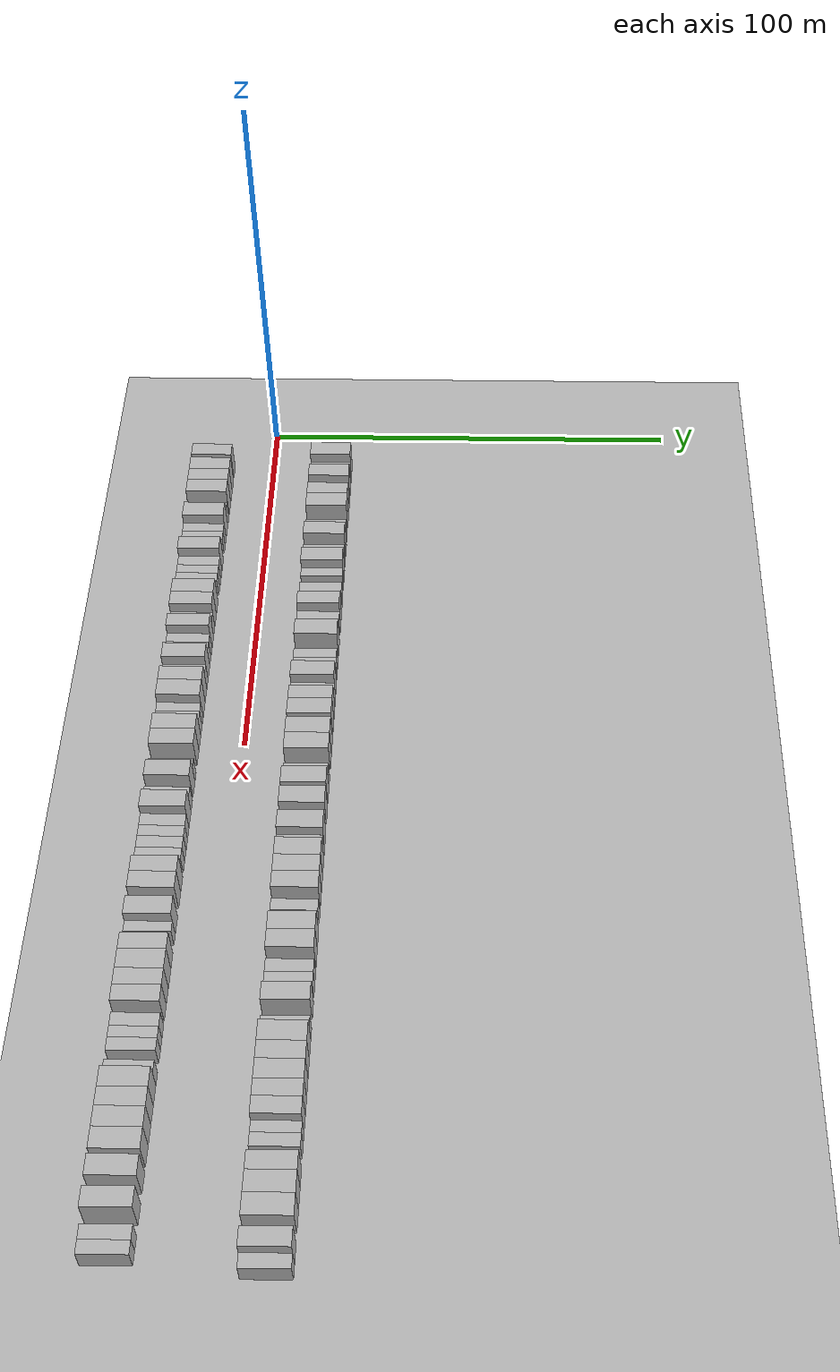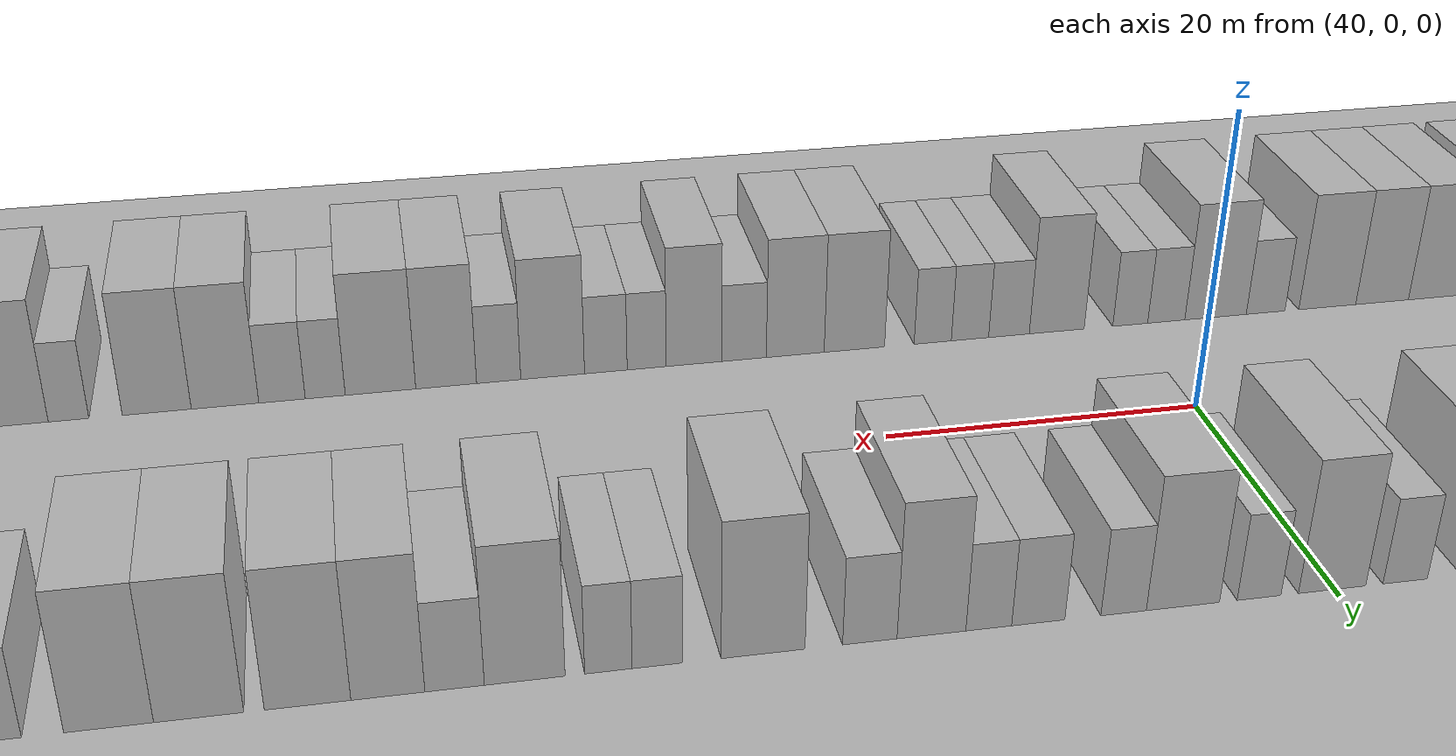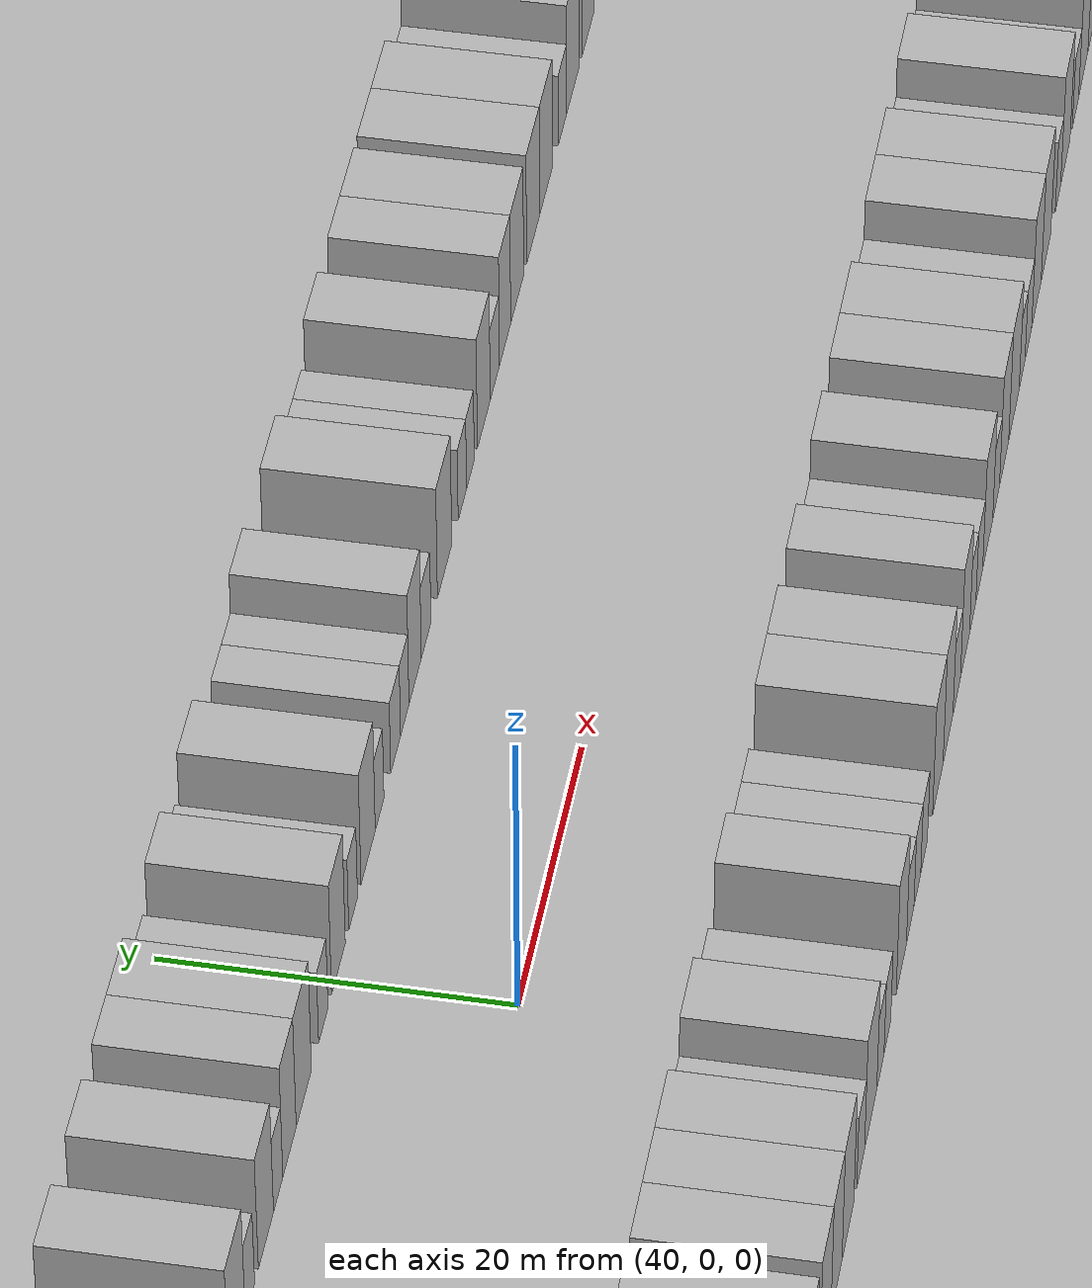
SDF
<?xml version="1.0" encoding="utf-8"?>

<sdf version="1.6">

   <world name="default">

      <gui fullscreen="0">

         <camera name="user_camera">

            <pose>-15 0 4.57585 0 0 0</pose>

            <view_controller>orbit</view_controller>

         </camera>

      </gui>

      <scene>

         <sky>

           <clouds>

             <speed>12</speed>

           </clouds>

         </sky>

         <ambient>0.4 0.4 0.4 1</ambient>

         <background>0.7 0.7 0.7 1</background>

         <shadows>1</shadows>

      </scene>

      <gravity>0 0 -9.8066</gravity>

      <magnetic_field>6e-06 2.3e-05 -4.2e-05</magnetic_field>

      <physics default="0" name="default_physics" type="ode">

         <ode>

            <solver>

               <type>quick</type>

               <iters>10</iters>

               <sor>1.0</sor>

               <use_dynamic_moi_rescaling>0</use_dynamic_moi_rescaling>

            </solver>

            <constraints>

               <cfm>0</cfm>

               <erp>0.2</erp>

               <contact_max_correcting_vel>100</contact_max_correcting_vel>

               <contact_surface_layer>0.001</contact_surface_layer>

            </constraints>

         </ode>

         <max_step_size>0.004</max_step_size>

         <real_time_factor>1</real_time_factor>

         <real_time_update_rate>250</real_time_update_rate>

      </physics>

      <light name="sun" type="directional">

         <cast_shadows>1</cast_shadows>

         <pose>0 0 10 0 0 0</pose>

         <diffuse>0.8 0.8 0.8 1</diffuse>

         <specular>0.2 0.2 0.2 1</specular>

         <attenuation>

            <range>1000</range>

            <constant>0.9</constant>

            <linear>0.01</linear>

            <quadratic>0.001</quadratic>

         </attenuation>

         <direction>-0.5 0.1 -0.9</direction>

      </light>

      <include>

         <name>ground_plane_1</name>

         <uri>model://HANNAS_ground_plane</uri>

         <pose>0 0 0  0 0 0</pose>

      </include>

      <include>

         <name>ground_plane_2</name>

         <uri>model://HANNAS_ground_plane</uri>

         <pose>100 0 0  0 0 0</pose>

      </include>

      <model name="building_1">

         <static>1</static>

         <pose frame="">13.1305 15.0000 0 0.000000 0.000000 1.570796</pose>

         <link name="link">

            <pose frame="">0 0 4.50 0 0 0</pose>

            <collision name="collision">

               <geometry>

                  <box>

                     <size>10.0000 4.2610 9.0000</size>

                  </box>

               </geometry>

               <max_contacts>10</max_contacts>

               <surface>

                  <contact>

                     <ode/>

                  </contact>

                  <bounce/>

                  <friction>

                     <torsional>

                        <ode/>

                     </torsional>

                     <ode/>

                  </friction>

               </surface>

            </collision>

            <visual name="visual">

               <cast_shadows>0</cast_shadows>

               <geometry>

                  <box>

                     <size>10.0000 4.2610 9.0000</size>

                  </box>

               </geometry>

               <material>

                  <script>

                     <uri>model://HANNAS_wall/materials/scripts</uri>

                     <uri>model://HANNAS_wall/materials/textures</uri>

                     <name>vrc/HANNAS_wall</name>

                  </script>

               </material>

            </visual>

            <self_collide>0</self_collide>

            <enable_wind>0</enable_wind>

            <kinematic>0</kinematic>

         </link>

      </model>

      <model name="building_2">

         <static>1</static>

         <pose frame="">16.4832 15.0000 0 0.000000 0.000000 1.570796</pose>

         <link name="link">

            <pose frame="">0 0 3.00 0 0 0</pose>

            <collision name="collision">

               <geometry>

                  <box>

                     <size>10.0000 2.4443 6.0000</size>

                  </box>

               </geometry>

               <max_contacts>10</max_contacts>

               <surface>

                  <contact>

                     <ode/>

                  </contact>

                  <bounce/>

                  <friction>

                     <torsional>

                        <ode/>

                     </torsional>

                     <ode/>

                  </friction>

               </surface>

            </collision>

            <visual name="visual">

               <cast_shadows>0</cast_shadows>

               <geometry>

                  <box>

                     <size>10.0000 2.4443 6.0000</size>

                  </box>

               </geometry>

               <material>

                  <script>

                     <uri>model://HANNAS_wall/materials/scripts</uri>

                     <uri>model://HANNAS_wall/materials/textures</uri>

                     <name>vrc/HANNAS_wall</name>

                  </script>

               </material>

            </visual>

            <self_collide>0</self_collide>

            <enable_wind>0</enable_wind>

            <kinematic>0</kinematic>

         </link>

      </model>

      <model name="building_3">

         <static>1</static>

         <pose frame="">20.7164 15.0000 0 0.000000 0.000000 1.570796</pose>

         <link name="link">

            <pose frame="">0 0 4.50 0 0 0</pose>

            <collision name="collision">

               <geometry>

                  <box>

                     <size>10.0000 4.0220 9.0000</size>

                  </box>

               </geometry>

               <max_contacts>10</max_contacts>

               <surface>

                  <contact>

                     <ode/>

                  </contact>

                  <bounce/>

                  <friction>

                     <torsional>

                        <ode/>

                     </torsional>

                     <ode/>

                  </friction>

               </surface>

            </collision>

            <visual name="visual">

               <cast_shadows>0</cast_shadows>

               <geometry>

                  <box>

                     <size>10.0000 4.0220 9.0000</size>

                  </box>

               </geometry>

               <material>

                  <script>

                     <uri>model://HANNAS_wall/materials/scripts</uri>

                     <uri>model://HANNAS_wall/materials/textures</uri>

                     <name>vrc/HANNAS_wall</name>

                  </script>

               </material>

            </visual>

            <self_collide>0</self_collide>

            <enable_wind>0</enable_wind>

            <kinematic>0</kinematic>

         </link>

      </model>

      <model name="building_4">

         <static>1</static>

         <pose frame="">23.9780 15.0000 0 0.000000 0.000000 1.570796</pose>

         <link name="link">

            <pose frame="">0 0 3.00 0 0 0</pose>

            <collision name="collision">

               <geometry>

                  <box>

                     <size>10.0000 2.5012 6.0000</size>

                  </box>

               </geometry>

               <max_contacts>10</max_contacts>

               <surface>

                  <contact>

                     <ode/>

                  </contact>

                  <bounce/>

                  <friction>

                     <torsional>

                        <ode/>

                     </torsional>

                     <ode/>

                  </friction>

               </surface>

            </collision>

            <visual name="visual">

               <cast_shadows>0</cast_shadows>

               <geometry>

                  <box>

                     <size>10.0000 2.5012 6.0000</size>

                  </box>

               </geometry>

               <material>

                  <script>

                     <uri>model://HANNAS_wall/materials/scripts</uri>

                     <uri>model://HANNAS_wall/materials/textures</uri>

                     <name>vrc/HANNAS_wall</name>

                  </script>

               </material>

            </visual>

            <self_collide>0</self_collide>

            <enable_wind>0</enable_wind>

            <kinematic>0</kinematic>

         </link>

      </model>

      <model name="building_5">

         <static>1</static>

         <pose frame="">27.0393 15.0000 0 0.000000 0.000000 1.570796</pose>

         <link name="link">

            <pose frame="">0 0 4.50 0 0 0</pose>

            <collision name="collision">

               <geometry>

                  <box>

                     <size>10.0000 3.6214 9.0000</size>

                  </box>

               </geometry>

               <max_contacts>10</max_contacts>

               <surface>

                  <contact>

                     <ode/>

                  </contact>

                  <bounce/>

                  <friction>

                     <torsional>

                        <ode/>

                     </torsional>

                     <ode/>

                  </friction>

               </surface>

            </collision>

            <visual name="visual">

               <cast_shadows>0</cast_shadows>

               <geometry>

                  <box>

                     <size>10.0000 3.6214 9.0000</size>

                  </box>

               </geometry>

               <material>

                  <script>

                     <uri>model://HANNAS_wall/materials/scripts</uri>

                     <uri>model://HANNAS_wall/materials/textures</uri>

                     <name>vrc/HANNAS_wall</name>

                  </script>

               </material>

            </visual>

            <self_collide>0</self_collide>

            <enable_wind>0</enable_wind>

            <kinematic>0</kinematic>

         </link>

      </model>

      <model name="building_6">

         <static>1</static>

         <pose frame="">30.9318 15.0000 0 0.000000 0.000000 1.570796</pose>

         <link name="link">

            <pose frame="">0 0 4.50 0 0 0</pose>

            <collision name="collision">

               <geometry>

                  <box>

                     <size>10.0000 4.1634 9.0000</size>

                  </box>

               </geometry>

               <max_contacts>10</max_contacts>

               <surface>

                  <contact>

                     <ode/>

                  </contact>

                  <bounce/>

                  <friction>

                     <torsional>

                        <ode/>

                     </torsional>

                     <ode/>

                  </friction>

               </surface>

            </collision>

            <visual name="visual">

               <cast_shadows>0</cast_shadows>

               <geometry>

                  <box>

                     <size>10.0000 4.1634 9.0000</size>

                  </box>

               </geometry>

               <material>

                  <script>

                     <uri>model://HANNAS_wall/materials/scripts</uri>

                     <uri>model://HANNAS_wall/materials/textures</uri>

                     <name>vrc/HANNAS_wall</name>

                  </script>

               </material>

            </visual>

            <self_collide>0</self_collide>

            <enable_wind>0</enable_wind>

            <kinematic>0</kinematic>

         </link>

      </model>

      <model name="building_7">

         <static>1</static>

         <pose frame="">36.3098 15.0000 0 0.000000 0.000000 1.570796</pose>

         <link name="link">

            <pose frame="">0 0 3.00 0 0 0</pose>

            <collision name="collision">

               <geometry>

                  <box>

                     <size>10.0000 2.5927 6.0000</size>

                  </box>

               </geometry>

               <max_contacts>10</max_contacts>

               <surface>

                  <contact>

                     <ode/>

                  </contact>

                  <bounce/>

                  <friction>

                     <torsional>

                        <ode/>

                     </torsional>

                     <ode/>

                  </friction>

               </surface>

            </collision>

            <visual name="visual">

               <cast_shadows>0</cast_shadows>

               <geometry>

                  <box>

                     <size>10.0000 2.5927 6.0000</size>

                  </box>

               </geometry>

               <material>

                  <script>

                     <uri>model://HANNAS_wall/materials/scripts</uri>

                     <uri>model://HANNAS_wall/materials/textures</uri>

                     <name>vrc/HANNAS_wall</name>

                  </script>

               </material>

            </visual>

            <self_collide>0</self_collide>

            <enable_wind>0</enable_wind>

            <kinematic>0</kinematic>

         </link>

      </model>

      <model name="building_8">

         <static>1</static>

         <pose frame="">40.5476 15.0000 0 0.000000 0.000000 1.570796</pose>

         <link name="link">

            <pose frame="">0 0 4.50 0 0 0</pose>

            <collision name="collision">

               <geometry>

                  <box>

                     <size>10.0000 3.8829 9.0000</size>

                  </box>

               </geometry>

               <max_contacts>10</max_contacts>

               <surface>

                  <contact>

                     <ode/>

                  </contact>

                  <bounce/>

                  <friction>

                     <torsional>

                        <ode/>

                     </torsional>

                     <ode/>

                  </friction>

               </surface>

            </collision>

            <visual name="visual">

               <cast_shadows>0</cast_shadows>

               <geometry>

                  <box>

                     <size>10.0000 3.8829 9.0000</size>

                  </box>

               </geometry>

               <material>

                  <script>

                     <uri>model://HANNAS_wall/materials/scripts</uri>

                     <uri>model://HANNAS_wall/materials/textures</uri>

                     <name>vrc/HANNAS_wall</name>

                  </script>

               </material>

            </visual>

            <self_collide>0</self_collide>

            <enable_wind>0</enable_wind>

            <kinematic>0</kinematic>

         </link>

      </model>

      <model name="building_9">

         <static>1</static>

         <pose frame="">44.7395 15.0000 0 0.000000 0.000000 1.570796</pose>

         <link name="link">

            <pose frame="">0 0 3.00 0 0 0</pose>

            <collision name="collision">

               <geometry>

                  <box>

                     <size>10.0000 2.5008 6.0000</size>

                  </box>

               </geometry>

               <max_contacts>10</max_contacts>

               <surface>

                  <contact>

                     <ode/>

                  </contact>

                  <bounce/>

                  <friction>

                     <torsional>

                        <ode/>

                     </torsional>

                     <ode/>

                  </friction>

               </surface>

            </collision>

            <visual name="visual">

               <cast_shadows>0</cast_shadows>

               <geometry>

                  <box>

                     <size>10.0000 2.5008 6.0000</size>

                  </box>

               </geometry>

               <material>

                  <script>

                     <uri>model://HANNAS_wall/materials/scripts</uri>

                     <uri>model://HANNAS_wall/materials/textures</uri>

                     <name>vrc/HANNAS_wall</name>

                  </script>

               </material>

            </visual>

            <self_collide>0</self_collide>

            <enable_wind>0</enable_wind>

            <kinematic>0</kinematic>

         </link>

      </model>

      <model name="building_10">

         <static>1</static>

         <pose frame="">49.0521 15.0000 0 0.000000 0.000000 1.570796</pose>

         <link name="link">

            <pose frame="">0 0 4.50 0 0 0</pose>

            <collision name="collision">

               <geometry>

                  <box>

                     <size>10.0000 4.1243 9.0000</size>

                  </box>

               </geometry>

               <max_contacts>10</max_contacts>

               <surface>

                  <contact>

                     <ode/>

                  </contact>

                  <bounce/>

                  <friction>

                     <torsional>

                        <ode/>

                     </torsional>

                     <ode/>

                  </friction>

               </surface>

            </collision>

            <visual name="visual">

               <cast_shadows>0</cast_shadows>

               <geometry>

                  <box>

                     <size>10.0000 4.1243 9.0000</size>

                  </box>

               </geometry>

               <material>

                  <script>

                     <uri>model://HANNAS_wall/materials/scripts</uri>

                     <uri>model://HANNAS_wall/materials/textures</uri>

                     <name>vrc/HANNAS_wall</name>

                  </script>

               </material>

            </visual>

            <self_collide>0</self_collide>

            <enable_wind>0</enable_wind>

            <kinematic>0</kinematic>

         </link>

      </model>

      <model name="building_11">

         <static>1</static>

         <pose frame="">52.3806 15.0000 0 0.000000 0.000000 1.570796</pose>

         <link name="link">

            <pose frame="">0 0 3.00 0 0 0</pose>

            <collision name="collision">

               <geometry>

                  <box>

                     <size>10.0000 2.5327 6.0000</size>

                  </box>

               </geometry>

               <max_contacts>10</max_contacts>

               <surface>

                  <contact>

                     <ode/>

                  </contact>

                  <bounce/>

                  <friction>

                     <torsional>

                        <ode/>

                     </torsional>

                     <ode/>

                  </friction>

               </surface>

            </collision>

            <visual name="visual">

               <cast_shadows>0</cast_shadows>

               <geometry>

                  <box>

                     <size>10.0000 2.5327 6.0000</size>

                  </box>

               </geometry>

               <material>

                  <script>

                     <uri>model://HANNAS_wall/materials/scripts</uri>

                     <uri>model://HANNAS_wall/materials/textures</uri>

                     <name>vrc/HANNAS_wall</name>

                  </script>

               </material>

            </visual>

            <self_collide>0</self_collide>

            <enable_wind>0</enable_wind>

            <kinematic>0</kinematic>

         </link>

      </model>

      <model name="building_12">

         <static>1</static>

         <pose frame="">57.1099 15.0000 0 0.000000 0.000000 1.570796</pose>

         <link name="link">

            <pose frame="">0 0 3.00 0 0 0</pose>

            <collision name="collision">

               <geometry>

                  <box>

                     <size>10.0000 2.9259 6.0000</size>

                  </box>

               </geometry>

               <max_contacts>10</max_contacts>

               <surface>

                  <contact>

                     <ode/>

                  </contact>

                  <bounce/>

                  <friction>

                     <torsional>

                        <ode/>

                     </torsional>

                     <ode/>

                  </friction>

               </surface>

            </collision>

            <visual name="visual">

               <cast_shadows>0</cast_shadows>

               <geometry>

                  <box>

                     <size>10.0000 2.9259 6.0000</size>

                  </box>

               </geometry>

               <material>

                  <script>

                     <uri>model://HANNAS_wall/materials/scripts</uri>

                     <uri>model://HANNAS_wall/materials/textures</uri>

                     <name>vrc/HANNAS_wall</name>

                  </script>

               </material>

            </visual>

            <self_collide>0</self_collide>

            <enable_wind>0</enable_wind>

            <kinematic>0</kinematic>

         </link>

      </model>

      <model name="building_13">

         <static>1</static>

         <pose frame="">59.8237 15.0000 0 0.000000 0.000000 1.570796</pose>

         <link name="link">

            <pose frame="">0 0 3.00 0 0 0</pose>

            <collision name="collision">

               <geometry>

                  <box>

                     <size>10.0000 2.5016 6.0000</size>

                  </box>

               </geometry>

               <max_contacts>10</max_contacts>

               <surface>

                  <contact>

                     <ode/>

                  </contact>

                  <bounce/>

                  <friction>

                     <torsional>

                        <ode/>

                     </torsional>

                     <ode/>

                  </friction>

               </surface>

            </collision>

            <visual name="visual">

               <cast_shadows>0</cast_shadows>

               <geometry>

                  <box>

                     <size>10.0000 2.5016 6.0000</size>

                  </box>

               </geometry>

               <material>

                  <script>

                     <uri>model://HANNAS_wall/materials/scripts</uri>

                     <uri>model://HANNAS_wall/materials/textures</uri>

                     <name>vrc/HANNAS_wall</name>

                  </script>

               </material>

            </visual>

            <self_collide>0</self_collide>

            <enable_wind>0</enable_wind>

            <kinematic>0</kinematic>

         </link>

      </model>

      <model name="building_14">

         <static>1</static>

         <pose frame="">62.9377 15.0000 0 0.000000 0.000000 1.570796</pose>

         <link name="link">

            <pose frame="">0 0 4.50 0 0 0</pose>

            <collision name="collision">

               <geometry>

                  <box>

                     <size>10.0000 3.7264 9.0000</size>

                  </box>

               </geometry>

               <max_contacts>10</max_contacts>

               <surface>

                  <contact>

                     <ode/>

                  </contact>

                  <bounce/>

                  <friction>

                     <torsional>

                        <ode/>

                     </torsional>

                     <ode/>

                  </friction>

               </surface>

            </collision>

            <visual name="visual">

               <cast_shadows>0</cast_shadows>

               <geometry>

                  <box>

                     <size>10.0000 3.7264 9.0000</size>

                  </box>

               </geometry>

               <material>

                  <script>

                     <uri>model://HANNAS_wall/materials/scripts</uri>

                     <uri>model://HANNAS_wall/materials/textures</uri>

                     <name>vrc/HANNAS_wall</name>

                  </script>

               </material>

            </visual>

            <self_collide>0</self_collide>

            <enable_wind>0</enable_wind>

            <kinematic>0</kinematic>

         </link>

      </model>

      <model name="building_15">

         <static>1</static>

         <pose frame="">66.2591 15.0000 0 0.000000 0.000000 1.570796</pose>

         <link name="link">

            <pose frame="">0 0 3.00 0 0 0</pose>

            <collision name="collision">

               <geometry>

                  <box>

                     <size>10.0000 2.9166 6.0000</size>

                  </box>

               </geometry>

               <max_contacts>10</max_contacts>

               <surface>

                  <contact>

                     <ode/>

                  </contact>

                  <bounce/>

                  <friction>

                     <torsional>

                        <ode/>

                     </torsional>

                     <ode/>

                  </friction>

               </surface>

            </collision>

            <visual name="visual">

               <cast_shadows>0</cast_shadows>

               <geometry>

                  <box>

                     <size>10.0000 2.9166 6.0000</size>

                  </box>

               </geometry>

               <material>

                  <script>

                     <uri>model://HANNAS_wall/materials/scripts</uri>

                     <uri>model://HANNAS_wall/materials/textures</uri>

                     <name>vrc/HANNAS_wall</name>

                  </script>

               </material>

            </visual>

            <self_collide>0</self_collide>

            <enable_wind>0</enable_wind>

            <kinematic>0</kinematic>

         </link>

      </model>

      <model name="building_16">

         <static>1</static>

         <pose frame="">71.9295 15.0000 0 0.000000 0.000000 1.570796</pose>

         <link name="link">

            <pose frame="">0 0 4.50 0 0 0</pose>

            <collision name="collision">

               <geometry>

                  <box>

                     <size>10.0000 4.4241 9.0000</size>

                  </box>

               </geometry>

               <max_contacts>10</max_contacts>

               <surface>

                  <contact>

                     <ode/>

                  </contact>

                  <bounce/>

                  <friction>

                     <torsional>

                        <ode/>

                     </torsional>

                     <ode/>

                  </friction>

               </surface>

            </collision>

            <visual name="visual">

               <cast_shadows>0</cast_shadows>

               <geometry>

                  <box>

                     <size>10.0000 4.4241 9.0000</size>

                  </box>

               </geometry>

               <material>

                  <script>

                     <uri>model://HANNAS_wall/materials/scripts</uri>

                     <uri>model://HANNAS_wall/materials/textures</uri>

                     <name>vrc/HANNAS_wall</name>

                  </script>

               </material>

            </visual>

            <self_collide>0</self_collide>

            <enable_wind>0</enable_wind>

            <kinematic>0</kinematic>

         </link>

      </model>

      <model name="building_17">

         <static>1</static>

         <pose frame="">77.4528 15.0000 0 0.000000 0.000000 1.570796</pose>

         <link name="link">

            <pose frame="">0 0 3.00 0 0 0</pose>

            <collision name="collision">

               <geometry>

                  <box>

                     <size>10.0000 2.6226 6.0000</size>

                  </box>

               </geometry>

               <max_contacts>10</max_contacts>

               <surface>

                  <contact>

                     <ode/>

                  </contact>

                  <bounce/>

                  <friction>

                     <torsional>

                        <ode/>

                     </torsional>

                     <ode/>

                  </friction>

               </surface>

            </collision>

            <visual name="visual">

               <cast_shadows>0</cast_shadows>

               <geometry>

                  <box>

                     <size>10.0000 2.6226 6.0000</size>

                  </box>

               </geometry>

               <material>

                  <script>

                     <uri>model://HANNAS_wall/materials/scripts</uri>

                     <uri>model://HANNAS_wall/materials/textures</uri>

                     <name>vrc/HANNAS_wall</name>

                  </script>

               </material>

            </visual>

            <self_collide>0</self_collide>

            <enable_wind>0</enable_wind>

            <kinematic>0</kinematic>

         </link>

      </model>

      <model name="building_18">

         <static>1</static>

         <pose frame="">79.9871 15.0000 0 0.000000 0.000000 1.570796</pose>

         <link name="link">

            <pose frame="">0 0 3.00 0 0 0</pose>

            <collision name="collision">

               <geometry>

                  <box>

                     <size>10.0000 2.4461 6.0000</size>

                  </box>

               </geometry>

               <max_contacts>10</max_contacts>

               <surface>

                  <contact>

                     <ode/>

                  </contact>

                  <bounce/>

                  <friction>

                     <torsional>

                        <ode/>

                     </torsional>

                     <ode/>

                  </friction>

               </surface>

            </collision>

            <visual name="visual">

               <cast_shadows>0</cast_shadows>

               <geometry>

                  <box>

                     <size>10.0000 2.4461 6.0000</size>

                  </box>

               </geometry>

               <material>

                  <script>

                     <uri>model://HANNAS_wall/materials/scripts</uri>

                     <uri>model://HANNAS_wall/materials/textures</uri>

                     <name>vrc/HANNAS_wall</name>

                  </script>

               </material>

            </visual>

            <self_collide>0</self_collide>

            <enable_wind>0</enable_wind>

            <kinematic>0</kinematic>

         </link>

      </model>

      <model name="building_19">

         <static>1</static>

         <pose frame="">84.2621 15.0000 0 0.000000 0.000000 1.570796</pose>

         <link name="link">

            <pose frame="">0 0 4.50 0 0 0</pose>

            <collision name="collision">

               <geometry>

                  <box>

                     <size>10.0000 4.1038 9.0000</size>

                  </box>

               </geometry>

               <max_contacts>10</max_contacts>

               <surface>

                  <contact>

                     <ode/>

                  </contact>

                  <bounce/>

                  <friction>

                     <torsional>

                        <ode/>

                     </torsional>

                     <ode/>

                  </friction>

               </surface>

            </collision>

            <visual name="visual">

               <cast_shadows>0</cast_shadows>

               <geometry>

                  <box>

                     <size>10.0000 4.1038 9.0000</size>

                  </box>

               </geometry>

               <material>

                  <script>

                     <uri>model://HANNAS_wall/materials/scripts</uri>

                     <uri>model://HANNAS_wall/materials/textures</uri>

                     <name>vrc/HANNAS_wall</name>

                  </script>

               </material>

            </visual>

            <self_collide>0</self_collide>

            <enable_wind>0</enable_wind>

            <kinematic>0</kinematic>

         </link>

      </model>

      <model name="building_20">

         <static>1</static>

         <pose frame="">87.8092 15.0000 0 0.000000 0.000000 1.570796</pose>

         <link name="link">

            <pose frame="">0 0 3.00 0 0 0</pose>

            <collision name="collision">

               <geometry>

                  <box>

                     <size>10.0000 2.9904 6.0000</size>

                  </box>

               </geometry>

               <max_contacts>10</max_contacts>

               <surface>

                  <contact>

                     <ode/>

                  </contact>

                  <bounce/>

                  <friction>

                     <torsional>

                        <ode/>

                     </torsional>

                     <ode/>

                  </friction>

               </surface>

            </collision>

            <visual name="visual">

               <cast_shadows>0</cast_shadows>

               <geometry>

                  <box>

                     <size>10.0000 2.9904 6.0000</size>

                  </box>

               </geometry>

               <material>

                  <script>

                     <uri>model://HANNAS_wall/materials/scripts</uri>

                     <uri>model://HANNAS_wall/materials/textures</uri>

                     <name>vrc/HANNAS_wall</name>

                  </script>

               </material>

            </visual>

            <self_collide>0</self_collide>

            <enable_wind>0</enable_wind>

            <kinematic>0</kinematic>

         </link>

      </model>

      <model name="building_21">

         <static>1</static>

         <pose frame="">91.1462 15.0000 0 0.000000 0.000000 1.570796</pose>

         <link name="link">

            <pose frame="">0 0 4.50 0 0 0</pose>

            <collision name="collision">

               <geometry>

                  <box>

                     <size>10.0000 3.6837 9.0000</size>

                  </box>

               </geometry>

               <max_contacts>10</max_contacts>

               <surface>

                  <contact>

                     <ode/>

                  </contact>

                  <bounce/>

                  <friction>

                     <torsional>

                        <ode/>

                     </torsional>

                     <ode/>

                  </friction>

               </surface>

            </collision>

            <visual name="visual">

               <cast_shadows>0</cast_shadows>

               <geometry>

                  <box>

                     <size>10.0000 3.6837 9.0000</size>

                  </box>

               </geometry>

               <material>

                  <script>

                     <uri>model://HANNAS_wall/materials/scripts</uri>

                     <uri>model://HANNAS_wall/materials/textures</uri>

                     <name>vrc/HANNAS_wall</name>

                  </script>

               </material>

            </visual>

            <self_collide>0</self_collide>

            <enable_wind>0</enable_wind>

            <kinematic>0</kinematic>

         </link>

      </model>

      <model name="building_22">

         <static>1</static>

         <pose frame="">95.1196 15.0000 0 0.000000 0.000000 1.570796</pose>

         <link name="link">

            <pose frame="">0 0 4.50 0 0 0</pose>

            <collision name="collision">

               <geometry>

                  <box>

                     <size>10.0000 4.2631 9.0000</size>

                  </box>

               </geometry>

               <max_contacts>10</max_contacts>

               <surface>

                  <contact>

                     <ode/>

                  </contact>

                  <bounce/>

                  <friction>

                     <torsional>

                        <ode/>

                     </torsional>

                     <ode/>

                  </friction>

               </surface>

            </collision>

            <visual name="visual">

               <cast_shadows>0</cast_shadows>

               <geometry>

                  <box>

                     <size>10.0000 4.2631 9.0000</size>

                  </box>

               </geometry>

               <material>

                  <script>

                     <uri>model://HANNAS_wall/materials/scripts</uri>

                     <uri>model://HANNAS_wall/materials/textures</uri>

                     <name>vrc/HANNAS_wall</name>

                  </script>

               </material>

            </visual>

            <self_collide>0</self_collide>

            <enable_wind>0</enable_wind>

            <kinematic>0</kinematic>

         </link>

      </model>

      <model name="building_23">

         <static>1</static>

         <pose frame="">100.4330 15.0000 0 0.000000 0.000000 1.570796</pose>

         <link name="link">

            <pose frame="">0 0 4.50 0 0 0</pose>

            <collision name="collision">

               <geometry>

                  <box>

                     <size>10.0000 4.3636 9.0000</size>

                  </box>

               </geometry>

               <max_contacts>10</max_contacts>

               <surface>

                  <contact>

                     <ode/>

                  </contact>

                  <bounce/>

                  <friction>

                     <torsional>

                        <ode/>

                     </torsional>

                     <ode/>

                  </friction>

               </surface>

            </collision>

            <visual name="visual">

               <cast_shadows>0</cast_shadows>

               <geometry>

                  <box>

                     <size>10.0000 4.3636 9.0000</size>

                  </box>

               </geometry>

               <material>

                  <script>

                     <uri>model://HANNAS_wall/materials/scripts</uri>

                     <uri>model://HANNAS_wall/materials/textures</uri>

                     <name>vrc/HANNAS_wall</name>

                  </script>

               </material>

            </visual>

            <self_collide>0</self_collide>

            <enable_wind>0</enable_wind>

            <kinematic>0</kinematic>

         </link>

      </model>

      <model name="building_24">

         <static>1</static>

         <pose frame="">104.7611 15.0000 0 0.000000 0.000000 1.570796</pose>

         <link name="link">

            <pose frame="">0 0 4.50 0 0 0</pose>

            <collision name="collision">

               <geometry>

                  <box>

                     <size>10.0000 4.2925 9.0000</size>

                  </box>

               </geometry>

               <max_contacts>10</max_contacts>

               <surface>

                  <contact>

                     <ode/>

                  </contact>

                  <bounce/>

                  <friction>

                     <torsional>

                        <ode/>

                     </torsional>

                     <ode/>

                  </friction>

               </surface>

            </collision>

            <visual name="visual">

               <cast_shadows>0</cast_shadows>

               <geometry>

                  <box>

                     <size>10.0000 4.2925 9.0000</size>

                  </box>

               </geometry>

               <material>

                  <script>

                     <uri>model://HANNAS_wall/materials/scripts</uri>

                     <uri>model://HANNAS_wall/materials/textures</uri>

                     <name>vrc/HANNAS_wall</name>

                  </script>

               </material>

            </visual>

            <self_collide>0</self_collide>

            <enable_wind>0</enable_wind>

            <kinematic>0</kinematic>

         </link>

      </model>

      <model name="building_25">

         <static>1</static>

         <pose frame="">110.3749 15.0000 0 0.000000 0.000000 1.570796</pose>

         <link name="link">

            <pose frame="">0 0 3.00 0 0 0</pose>

            <collision name="collision">

               <geometry>

                  <box>

                     <size>10.0000 2.9353 6.0000</size>

                  </box>

               </geometry>

               <max_contacts>10</max_contacts>

               <surface>

                  <contact>

                     <ode/>

                  </contact>

                  <bounce/>

                  <friction>

                     <torsional>

                        <ode/>

                     </torsional>

                     <ode/>

                  </friction>

               </surface>

            </collision>

            <visual name="visual">

               <cast_shadows>0</cast_shadows>

               <geometry>

                  <box>

                     <size>10.0000 2.9353 6.0000</size>

                  </box>

               </geometry>

               <material>

                  <script>

                     <uri>model://HANNAS_wall/materials/scripts</uri>

                     <uri>model://HANNAS_wall/materials/textures</uri>

                     <name>vrc/HANNAS_wall</name>

                  </script>

               </material>

            </visual>

            <self_collide>0</self_collide>

            <enable_wind>0</enable_wind>

            <kinematic>0</kinematic>

         </link>

      </model>

      <model name="building_26">

         <static>1</static>

         <pose frame="">113.9571 15.0000 0 0.000000 0.000000 1.570796</pose>

         <link name="link">

            <pose frame="">0 0 4.50 0 0 0</pose>

            <collision name="collision">

               <geometry>

                  <box>

                     <size>10.0000 4.2290 9.0000</size>

                  </box>

               </geometry>

               <max_contacts>10</max_contacts>

               <surface>

                  <contact>

                     <ode/>

                  </contact>

                  <bounce/>

                  <friction>

                     <torsional>

                        <ode/>

                     </torsional>

                     <ode/>

                  </friction>

               </surface>

            </collision>

            <visual name="visual">

               <cast_shadows>0</cast_shadows>

               <geometry>

                  <box>

                     <size>10.0000 4.2290 9.0000</size>

                  </box>

               </geometry>

               <material>

                  <script>

                     <uri>model://HANNAS_wall/materials/scripts</uri>

                     <uri>model://HANNAS_wall/materials/textures</uri>

                     <name>vrc/HANNAS_wall</name>

                  </script>

               </material>

            </visual>

            <self_collide>0</self_collide>

            <enable_wind>0</enable_wind>

            <kinematic>0</kinematic>

         </link>

      </model>

      <model name="building_27">

         <static>1</static>

         <pose frame="">119.2484 15.0000 0 0.000000 0.000000 1.570796</pose>

         <link name="link">

            <pose frame="">0 0 4.50 0 0 0</pose>

            <collision name="collision">

               <geometry>

                  <box>

                     <size>10.0000 4.3536 9.0000</size>

                  </box>

               </geometry>

               <max_contacts>10</max_contacts>

               <surface>

                  <contact>

                     <ode/>

                  </contact>

                  <bounce/>

                  <friction>

                     <torsional>

                        <ode/>

                     </torsional>

                     <ode/>

                  </friction>

               </surface>

            </collision>

            <visual name="visual">

               <cast_shadows>0</cast_shadows>

               <geometry>

                  <box>

                     <size>10.0000 4.3536 9.0000</size>

                  </box>

               </geometry>

               <material>

                  <script>

                     <uri>model://HANNAS_wall/materials/scripts</uri>

                     <uri>model://HANNAS_wall/materials/textures</uri>

                     <name>vrc/HANNAS_wall</name>

                  </script>

               </material>

            </visual>

            <self_collide>0</self_collide>

            <enable_wind>0</enable_wind>

            <kinematic>0</kinematic>

         </link>

      </model>

      <model name="building_28">

         <static>1</static>

         <pose frame="">125.6580 15.0000 0 0.000000 0.000000 1.570796</pose>

         <link name="link">

            <pose frame="">0 0 4.50 0 0 0</pose>

            <collision name="collision">

               <geometry>

                  <box>

                     <size>10.0000 4.4658 9.0000</size>

                  </box>

               </geometry>

               <max_contacts>10</max_contacts>

               <surface>

                  <contact>

                     <ode/>

                  </contact>

                  <bounce/>

                  <friction>

                     <torsional>

                        <ode/>

                     </torsional>

                     <ode/>

                  </friction>

               </surface>

            </collision>

            <visual name="visual">

               <cast_shadows>0</cast_shadows>

               <geometry>

                  <box>

                     <size>10.0000 4.4658 9.0000</size>

                  </box>

               </geometry>

               <material>

                  <script>

                     <uri>model://HANNAS_wall/materials/scripts</uri>

                     <uri>model://HANNAS_wall/materials/textures</uri>

                     <name>vrc/HANNAS_wall</name>

                  </script>

               </material>

            </visual>

            <self_collide>0</self_collide>

            <enable_wind>0</enable_wind>

            <kinematic>0</kinematic>

         </link>

      </model>

      <model name="building_29">

         <static>1</static>

         <pose frame="">129.1652 15.0000 0 0.000000 0.000000 1.570796</pose>

         <link name="link">

            <pose frame="">0 0 3.00 0 0 0</pose>

            <collision name="collision">

               <geometry>

                  <box>

                     <size>10.0000 2.5487 6.0000</size>

                  </box>

               </geometry>

               <max_contacts>10</max_contacts>

               <surface>

                  <contact>

                     <ode/>

                  </contact>

                  <bounce/>

                  <friction>

                     <torsional>

                        <ode/>

                     </torsional>

                     <ode/>

                  </friction>

               </surface>

            </collision>

            <visual name="visual">

               <cast_shadows>0</cast_shadows>

               <geometry>

                  <box>

                     <size>10.0000 2.5487 6.0000</size>

                  </box>

               </geometry>

               <material>

                  <script>

                     <uri>model://HANNAS_wall/materials/scripts</uri>

                     <uri>model://HANNAS_wall/materials/textures</uri>

                     <name>vrc/HANNAS_wall</name>

                  </script>

               </material>

            </visual>

            <self_collide>0</self_collide>

            <enable_wind>0</enable_wind>

            <kinematic>0</kinematic>

         </link>

      </model>

      <model name="building_30">

         <static>1</static>

         <pose frame="">132.5843 15.0000 0 0.000000 0.000000 1.570796</pose>

         <link name="link">

            <pose frame="">0 0 4.50 0 0 0</pose>

            <collision name="collision">

               <geometry>

                  <box>

                     <size>10.0000 4.2895 9.0000</size>

                  </box>

               </geometry>

               <max_contacts>10</max_contacts>

               <surface>

                  <contact>

                     <ode/>

                  </contact>

                  <bounce/>

                  <friction>

                     <torsional>

                        <ode/>

                     </torsional>

                     <ode/>

                  </friction>

               </surface>

            </collision>

            <visual name="visual">

               <cast_shadows>0</cast_shadows>

               <geometry>

                  <box>

                     <size>10.0000 4.2895 9.0000</size>

                  </box>

               </geometry>

               <material>

                  <script>

                     <uri>model://HANNAS_wall/materials/scripts</uri>

                     <uri>model://HANNAS_wall/materials/textures</uri>

                     <name>vrc/HANNAS_wall</name>

                  </script>

               </material>

            </visual>

            <self_collide>0</self_collide>

            <enable_wind>0</enable_wind>

            <kinematic>0</kinematic>

         </link>

      </model>

      <model name="building_31">

         <static>1</static>

         <pose frame="">136.7707 15.0000 0 0.000000 0.000000 1.570796</pose>

         <link name="link">

            <pose frame="">0 0 4.50 0 0 0</pose>

            <collision name="collision">

               <geometry>

                  <box>

                     <size>10.0000 4.0835 9.0000</size>

                  </box>

               </geometry>

               <max_contacts>10</max_contacts>

               <surface>

                  <contact>

                     <ode/>

                  </contact>

                  <bounce/>

                  <friction>

                     <torsional>

                        <ode/>

                     </torsional>

                     <ode/>

                  </friction>

               </surface>

            </collision>

            <visual name="visual">

               <cast_shadows>0</cast_shadows>

               <geometry>

                  <box>

                     <size>10.0000 4.0835 9.0000</size>

                  </box>

               </geometry>

               <material>

                  <script>

                     <uri>model://HANNAS_wall/materials/scripts</uri>

                     <uri>model://HANNAS_wall/materials/textures</uri>

                     <name>vrc/HANNAS_wall</name>

                  </script>

               </material>

            </visual>

            <self_collide>0</self_collide>

            <enable_wind>0</enable_wind>

            <kinematic>0</kinematic>

         </link>

      </model>

      <model name="building_32">

         <static>1</static>

         <pose frame="">140.8305 15.0000 0 0.000000 0.000000 1.570796</pose>

         <link name="link">

            <pose frame="">0 0 4.50 0 0 0</pose>

            <collision name="collision">

               <geometry>

                  <box>

                     <size>10.0000 4.0360 9.0000</size>

                  </box>

               </geometry>

               <max_contacts>10</max_contacts>

               <surface>

                  <contact>

                     <ode/>

                  </contact>

                  <bounce/>

                  <friction>

                     <torsional>

                        <ode/>

                     </torsional>

                     <ode/>

                  </friction>

               </surface>

            </collision>

            <visual name="visual">

               <cast_shadows>0</cast_shadows>

               <geometry>

                  <box>

                     <size>10.0000 4.0360 9.0000</size>

                  </box>

               </geometry>

               <material>

                  <script>

                     <uri>model://HANNAS_wall/materials/scripts</uri>

                     <uri>model://HANNAS_wall/materials/textures</uri>

                     <name>vrc/HANNAS_wall</name>

                  </script>

               </material>

            </visual>

            <self_collide>0</self_collide>

            <enable_wind>0</enable_wind>

            <kinematic>0</kinematic>

         </link>

      </model>

      <model name="building_33">

         <static>1</static>

         <pose frame="">145.2298 15.0000 0 0.000000 0.000000 1.570796</pose>

         <link name="link">

            <pose frame="">0 0 3.00 0 0 0</pose>

            <collision name="collision">

               <geometry>

                  <box>

                     <size>10.0000 2.7626 6.0000</size>

                  </box>

               </geometry>

               <max_contacts>10</max_contacts>

               <surface>

                  <contact>

                     <ode/>

                  </contact>

                  <bounce/>

                  <friction>

                     <torsional>

                        <ode/>

                     </torsional>

                     <ode/>

                  </friction>

               </surface>

            </collision>

            <visual name="visual">

               <cast_shadows>0</cast_shadows>

               <geometry>

                  <box>

                     <size>10.0000 2.7626 6.0000</size>

                  </box>

               </geometry>

               <material>

                  <script>

                     <uri>model://HANNAS_wall/materials/scripts</uri>

                     <uri>model://HANNAS_wall/materials/textures</uri>

                     <name>vrc/HANNAS_wall</name>

                  </script>

               </material>

            </visual>

            <self_collide>0</self_collide>

            <enable_wind>0</enable_wind>

            <kinematic>0</kinematic>

         </link>

      </model>

      <model name="building_34">

         <static>1</static>

         <pose frame="">150.7208 15.0000 0 0.000000 0.000000 1.570796</pose>

         <link name="link">

            <pose frame="">0 0 4.50 0 0 0</pose>

            <collision name="collision">

               <geometry>

                  <box>

                     <size>10.0000 4.2193 9.0000</size>

                  </box>

               </geometry>

               <max_contacts>10</max_contacts>

               <surface>

                  <contact>

                     <ode/>

                  </contact>

                  <bounce/>

                  <friction>

                     <torsional>

                        <ode/>

                     </torsional>

                     <ode/>

                  </friction>

               </surface>

            </collision>

            <visual name="visual">

               <cast_shadows>0</cast_shadows>

               <geometry>

                  <box>

                     <size>10.0000 4.2193 9.0000</size>

                  </box>

               </geometry>

               <material>

                  <script>

                     <uri>model://HANNAS_wall/materials/scripts</uri>

                     <uri>model://HANNAS_wall/materials/textures</uri>

                     <name>vrc/HANNAS_wall</name>

                  </script>

               </material>

            </visual>

            <self_collide>0</self_collide>

            <enable_wind>0</enable_wind>

            <kinematic>0</kinematic>

         </link>

      </model>

      <model name="building_35">

         <static>1</static>

         <pose frame="">154.9682 15.0000 0 0.000000 0.000000 1.570796</pose>

         <link name="link">

            <pose frame="">0 0 4.50 0 0 0</pose>

            <collision name="collision">

               <geometry>

                  <box>

                     <size>10.0000 4.2756 9.0000</size>

                  </box>

               </geometry>

               <max_contacts>10</max_contacts>

               <surface>

                  <contact>

                     <ode/>

                  </contact>

                  <bounce/>

                  <friction>

                     <torsional>

                        <ode/>

                     </torsional>

                     <ode/>

                  </friction>

               </surface>

            </collision>

            <visual name="visual">

               <cast_shadows>0</cast_shadows>

               <geometry>

                  <box>

                     <size>10.0000 4.2756 9.0000</size>

                  </box>

               </geometry>

               <material>

                  <script>

                     <uri>model://HANNAS_wall/materials/scripts</uri>

                     <uri>model://HANNAS_wall/materials/textures</uri>

                     <name>vrc/HANNAS_wall</name>

                  </script>

               </material>

            </visual>

            <self_collide>0</self_collide>

            <enable_wind>0</enable_wind>

            <kinematic>0</kinematic>

         </link>

      </model>

      <model name="building_36">

         <static>1</static>

         <pose frame="">159.6041 15.0000 0 0.000000 0.000000 1.570796</pose>

         <link name="link">

            <pose frame="">0 0 3.00 0 0 0</pose>

            <collision name="collision">

               <geometry>

                  <box>

                     <size>10.0000 2.9961 6.0000</size>

                  </box>

               </geometry>

               <max_contacts>10</max_contacts>

               <surface>

                  <contact>

                     <ode/>

                  </contact>

                  <bounce/>

                  <friction>

                     <torsional>

                        <ode/>

                     </torsional>

                     <ode/>

                  </friction>

               </surface>

            </collision>

            <visual name="visual">

               <cast_shadows>0</cast_shadows>

               <geometry>

                  <box>

                     <size>10.0000 2.9961 6.0000</size>

                  </box>

               </geometry>

               <material>

                  <script>

                     <uri>model://HANNAS_wall/materials/scripts</uri>

                     <uri>model://HANNAS_wall/materials/textures</uri>

                     <name>vrc/HANNAS_wall</name>

                  </script>

               </material>

            </visual>

            <self_collide>0</self_collide>

            <enable_wind>0</enable_wind>

            <kinematic>0</kinematic>

         </link>

      </model>

      <model name="building_37">

         <static>1</static>

         <pose frame="">162.5634 15.0000 0 0.000000 0.000000 1.570796</pose>

         <link name="link">

            <pose frame="">0 0 3.00 0 0 0</pose>

            <collision name="collision">

               <geometry>

                  <box>

                     <size>10.0000 2.9226 6.0000</size>

                  </box>

               </geometry>

               <max_contacts>10</max_contacts>

               <surface>

                  <contact>

                     <ode/>

                  </contact>

                  <bounce/>

                  <friction>

                     <torsional>

                        <ode/>

                     </torsional>

                     <ode/>

                  </friction>

               </surface>

            </collision>

            <visual name="visual">

               <cast_shadows>0</cast_shadows>

               <geometry>

                  <box>

                     <size>10.0000 2.9226 6.0000</size>

                  </box>

               </geometry>

               <material>

                  <script>

                     <uri>model://HANNAS_wall/materials/scripts</uri>

                     <uri>model://HANNAS_wall/materials/textures</uri>

                     <name>vrc/HANNAS_wall</name>

                  </script>

               </material>

            </visual>

            <self_collide>0</self_collide>

            <enable_wind>0</enable_wind>

            <kinematic>0</kinematic>

         </link>

      </model>

      <model name="building_38">

         <static>1</static>

         <pose frame="">167.0217 15.0000 0 0.000000 0.000000 1.570796</pose>

         <link name="link">

            <pose frame="">0 0 4.50 0 0 0</pose>

            <collision name="collision">

               <geometry>

                  <box>

                     <size>10.0000 3.9940 9.0000</size>

                  </box>

               </geometry>

               <max_contacts>10</max_contacts>

               <surface>

                  <contact>

                     <ode/>

                  </contact>

                  <bounce/>

                  <friction>

                     <torsional>

                        <ode/>

                     </torsional>

                     <ode/>

                  </friction>

               </surface>

            </collision>

            <visual name="visual">

               <cast_shadows>0</cast_shadows>

               <geometry>

                  <box>

                     <size>10.0000 3.9940 9.0000</size>

                  </box>

               </geometry>

               <material>

                  <script>

                     <uri>model://HANNAS_wall/materials/scripts</uri>

                     <uri>model://HANNAS_wall/materials/textures</uri>

                     <name>vrc/HANNAS_wall</name>

                  </script>

               </material>

            </visual>

            <self_collide>0</self_collide>

            <enable_wind>0</enable_wind>

            <kinematic>0</kinematic>

         </link>

      </model>

      <model name="building_39">

         <static>1</static>

         <pose frame="">172.2708 15.0000 0 0.000000 0.000000 1.570796</pose>

         <link name="link">

            <pose frame="">0 0 3.00 0 0 0</pose>

            <collision name="collision">

               <geometry>

                  <box>

                     <size>10.0000 2.5043 6.0000</size>

                  </box>

               </geometry>

               <max_contacts>10</max_contacts>

               <surface>

                  <contact>

                     <ode/>

                  </contact>

                  <bounce/>

                  <friction>

                     <torsional>

                        <ode/>

                     </torsional>

                     <ode/>

                  </friction>

               </surface>

            </collision>

            <visual name="visual">

               <cast_shadows>0</cast_shadows>

               <geometry>

                  <box>

                     <size>10.0000 2.5043 6.0000</size>

                  </box>

               </geometry>

               <material>

                  <script>

                     <uri>model://HANNAS_wall/materials/scripts</uri>

                     <uri>model://HANNAS_wall/materials/textures</uri>

                     <name>vrc/HANNAS_wall</name>

                  </script>

               </material>

            </visual>

            <self_collide>0</self_collide>

            <enable_wind>0</enable_wind>

            <kinematic>0</kinematic>

         </link>

      </model>

      <model name="building_40">

         <static>1</static>

         <pose frame="">175.7442 15.0000 0 0.000000 0.000000 1.570796</pose>

         <link name="link">

            <pose frame="">0 0 4.50 0 0 0</pose>

            <collision name="collision">

               <geometry>

                  <box>

                     <size>10.0000 4.4425 9.0000</size>

                  </box>

               </geometry>

               <max_contacts>10</max_contacts>

               <surface>

                  <contact>

                     <ode/>

                  </contact>

                  <bounce/>

                  <friction>

                     <torsional>

                        <ode/>

                     </torsional>

                     <ode/>

                  </friction>

               </surface>

            </collision>

            <visual name="visual">

               <cast_shadows>0</cast_shadows>

               <geometry>

                  <box>

                     <size>10.0000 4.4425 9.0000</size>

                  </box>

               </geometry>

               <material>

                  <script>

                     <uri>model://HANNAS_wall/materials/scripts</uri>

                     <uri>model://HANNAS_wall/materials/textures</uri>

                     <name>vrc/HANNAS_wall</name>

                  </script>

               </material>

            </visual>

            <self_collide>0</self_collide>

            <enable_wind>0</enable_wind>

            <kinematic>0</kinematic>

         </link>

      </model>

      <model name="building_41">

         <static>1</static>

         <pose frame="">179.9159 15.0000 0 0.000000 0.000000 1.570796</pose>

         <link name="link">

            <pose frame="">0 0 4.50 0 0 0</pose>

            <collision name="collision">

               <geometry>

                  <box>

                     <size>10.0000 3.9008 9.0000</size>

                  </box>

               </geometry>

               <max_contacts>10</max_contacts>

               <surface>

                  <contact>

                     <ode/>

                  </contact>

                  <bounce/>

                  <friction>

                     <torsional>

                        <ode/>

                     </torsional>

                     <ode/>

                  </friction>

               </surface>

            </collision>

            <visual name="visual">

               <cast_shadows>0</cast_shadows>

               <geometry>

                  <box>

                     <size>10.0000 3.9008 9.0000</size>

                  </box>

               </geometry>

               <material>

                  <script>

                     <uri>model://HANNAS_wall/materials/scripts</uri>

                     <uri>model://HANNAS_wall/materials/textures</uri>

                     <name>vrc/HANNAS_wall</name>

                  </script>

               </material>

            </visual>

            <self_collide>0</self_collide>

            <enable_wind>0</enable_wind>

            <kinematic>0</kinematic>

         </link>

      </model>

      <model name="building_42">

         <static>1</static>

         <pose frame="">183.9827 15.0000 0 0.000000 0.000000 1.570796</pose>

         <link name="link">

            <pose frame="">0 0 4.50 0 0 0</pose>

            <collision name="collision">

               <geometry>

                  <box>

                     <size>10.0000 4.2328 9.0000</size>

                  </box>

               </geometry>

               <max_contacts>10</max_contacts>

               <surface>

                  <contact>

                     <ode/>

                  </contact>

                  <bounce/>

                  <friction>

                     <torsional>

                        <ode/>

                     </torsional>

                     <ode/>

                  </friction>

               </surface>

            </collision>

            <visual name="visual">

               <cast_shadows>0</cast_shadows>

               <geometry>

                  <box>

                     <size>10.0000 4.2328 9.0000</size>

                  </box>

               </geometry>

               <material>

                  <script>

                     <uri>model://HANNAS_wall/materials/scripts</uri>

                     <uri>model://HANNAS_wall/materials/textures</uri>

                     <name>vrc/HANNAS_wall</name>

                  </script>

               </material>

            </visual>

            <self_collide>0</self_collide>

            <enable_wind>0</enable_wind>

            <kinematic>0</kinematic>

         </link>

      </model>

      <model name="building_43">

         <static>1</static>

         <pose frame="">187.9259 15.0000 0 0.000000 0.000000 1.570796</pose>

         <link name="link">

            <pose frame="">0 0 4.50 0 0 0</pose>

            <collision name="collision">

               <geometry>

                  <box>

                     <size>10.0000 3.6535 9.0000</size>

                  </box>

               </geometry>

               <max_contacts>10</max_contacts>

               <surface>

                  <contact>

                     <ode/>

                  </contact>

                  <bounce/>

                  <friction>

                     <torsional>

                        <ode/>

                     </torsional>

                     <ode/>

                  </friction>

               </surface>

            </collision>

            <visual name="visual">

               <cast_shadows>0</cast_shadows>

               <geometry>

                  <box>

                     <size>10.0000 3.6535 9.0000</size>

                  </box>

               </geometry>

               <material>

                  <script>

                     <uri>model://HANNAS_wall/materials/scripts</uri>

                     <uri>model://HANNAS_wall/materials/textures</uri>

                     <name>vrc/HANNAS_wall</name>

                  </script>

               </material>

            </visual>

            <self_collide>0</self_collide>

            <enable_wind>0</enable_wind>

            <kinematic>0</kinematic>

         </link>

      </model>

      <model name="building_44">

         <static>1</static>

         <pose frame="">191.5947 15.0000 0 0.000000 0.000000 1.570796</pose>

         <link name="link">

            <pose frame="">0 0 4.50 0 0 0</pose>

            <collision name="collision">

               <geometry>

                  <box>

                     <size>10.0000 3.6842 9.0000</size>

                  </box>

               </geometry>

               <max_contacts>10</max_contacts>

               <surface>

                  <contact>

                     <ode/>

                  </contact>

                  <bounce/>

                  <friction>

                     <torsional>

                        <ode/>

                     </torsional>

                     <ode/>

                  </friction>

               </surface>

            </collision>

            <visual name="visual">

               <cast_shadows>0</cast_shadows>

               <geometry>

                  <box>

                     <size>10.0000 3.6842 9.0000</size>

                  </box>

               </geometry>

               <material>

                  <script>

                     <uri>model://HANNAS_wall/materials/scripts</uri>

                     <uri>model://HANNAS_wall/materials/textures</uri>

                     <name>vrc/HANNAS_wall</name>

                  </script>

               </material>

            </visual>

            <self_collide>0</self_collide>

            <enable_wind>0</enable_wind>

            <kinematic>0</kinematic>

         </link>

      </model>

      <model name="building_45">

         <static>1</static>

         <pose frame="">194.6603 15.0000 0 0.000000 0.000000 1.570796</pose>

         <link name="link">

            <pose frame="">0 0 3.00 0 0 0</pose>

            <collision name="collision">

               <geometry>

                  <box>

                     <size>10.0000 2.4469 6.0000</size>

                  </box>

               </geometry>

               <max_contacts>10</max_contacts>

               <surface>

                  <contact>

                     <ode/>

                  </contact>

                  <bounce/>

                  <friction>

                     <torsional>

                        <ode/>

                     </torsional>

                     <ode/>

                  </friction>

               </surface>

            </collision>

            <visual name="visual">

               <cast_shadows>0</cast_shadows>

               <geometry>

                  <box>

                     <size>10.0000 2.4469 6.0000</size>

                  </box>

               </geometry>

               <material>

                  <script>

                     <uri>model://HANNAS_wall/materials/scripts</uri>

                     <uri>model://HANNAS_wall/materials/textures</uri>

                     <name>vrc/HANNAS_wall</name>

                  </script>

               </material>

            </visual>

            <self_collide>0</self_collide>

            <enable_wind>0</enable_wind>

            <kinematic>0</kinematic>

         </link>

      </model>

      <model name="building_46">

         <static>1</static>

         <pose frame="">197.3124 15.0000 0 0.000000 0.000000 1.570796</pose>

         <link name="link">

            <pose frame="">0 0 3.00 0 0 0</pose>

            <collision name="collision">

               <geometry>

                  <box>

                     <size>10.0000 2.8573 6.0000</size>

                  </box>

               </geometry>

               <max_contacts>10</max_contacts>

               <surface>

                  <contact>

                     <ode/>

                  </contact>

                  <bounce/>

                  <friction>

                     <torsional>

                        <ode/>

                     </torsional>

                     <ode/>

                  </friction>

               </surface>

            </collision>

            <visual name="visual">

               <cast_shadows>0</cast_shadows>

               <geometry>

                  <box>

                     <size>10.0000 2.8573 6.0000</size>

                  </box>

               </geometry>

               <material>

                  <script>

                     <uri>model://HANNAS_wall/materials/scripts</uri>

                     <uri>model://HANNAS_wall/materials/textures</uri>

                     <name>vrc/HANNAS_wall</name>

                  </script>

               </material>

            </visual>

            <self_collide>0</self_collide>

            <enable_wind>0</enable_wind>

            <kinematic>0</kinematic>

         </link>

      </model>

      <model name="building_47">

         <static>1</static>

         <pose frame="">202.6811 15.0000 0 0.000000 0.000000 1.570796</pose>

         <link name="link">

            <pose frame="">0 0 4.50 0 0 0</pose>

            <collision name="collision">

               <geometry>

                  <box>

                     <size>10.0000 3.8801 9.0000</size>

                  </box>

               </geometry>

               <max_contacts>10</max_contacts>

               <surface>

                  <contact>

                     <ode/>

                  </contact>

                  <bounce/>

                  <friction>

                     <torsional>

                        <ode/>

                     </torsional>

                     <ode/>

                  </friction>

               </surface>

            </collision>

            <visual name="visual">

               <cast_shadows>0</cast_shadows>

               <geometry>

                  <box>

                     <size>10.0000 3.8801 9.0000</size>

                  </box>

               </geometry>

               <material>

                  <script>

                     <uri>model://HANNAS_wall/materials/scripts</uri>

                     <uri>model://HANNAS_wall/materials/textures</uri>

                     <name>vrc/HANNAS_wall</name>

                  </script>

               </material>

            </visual>

            <self_collide>0</self_collide>

            <enable_wind>0</enable_wind>

            <kinematic>0</kinematic>

         </link>

      </model>

      <model name="building_48">

         <static>1</static>

         <pose frame="">206.8475 15.0000 0 0.000000 0.000000 1.570796</pose>

         <link name="link">

            <pose frame="">0 0 4.50 0 0 0</pose>

            <collision name="collision">

               <geometry>

                  <box>

                     <size>10.0000 4.4528 9.0000</size>

                  </box>

               </geometry>

               <max_contacts>10</max_contacts>

               <surface>

                  <contact>

                     <ode/>

                  </contact>

                  <bounce/>

                  <friction>

                     <torsional>

                        <ode/>

                     </torsional>

                     <ode/>

                  </friction>

               </surface>

            </collision>

            <visual name="visual">

               <cast_shadows>0</cast_shadows>

               <geometry>

                  <box>

                     <size>10.0000 4.4528 9.0000</size>

                  </box>

               </geometry>

               <material>

                  <script>

                     <uri>model://HANNAS_wall/materials/scripts</uri>

                     <uri>model://HANNAS_wall/materials/textures</uri>

                     <name>vrc/HANNAS_wall</name>

                  </script>

               </material>

            </visual>

            <self_collide>0</self_collide>

            <enable_wind>0</enable_wind>

            <kinematic>0</kinematic>

         </link>

      </model>

      <model name="building_49">

         <static>1</static>

         <pose frame="">211.3017 15.0000 0 0.000000 0.000000 1.570796</pose>

         <link name="link">

            <pose frame="">0 0 4.50 0 0 0</pose>

            <collision name="collision">

               <geometry>

                  <box>

                     <size>10.0000 4.4556 9.0000</size>

                  </box>

               </geometry>

               <max_contacts>10</max_contacts>

               <surface>

                  <contact>

                     <ode/>

                  </contact>

                  <bounce/>

                  <friction>

                     <torsional>

                        <ode/>

                     </torsional>

                     <ode/>

                  </friction>

               </surface>

            </collision>

            <visual name="visual">

               <cast_shadows>0</cast_shadows>

               <geometry>

                  <box>

                     <size>10.0000 4.4556 9.0000</size>

                  </box>

               </geometry>

               <material>

                  <script>

                     <uri>model://HANNAS_wall/materials/scripts</uri>

                     <uri>model://HANNAS_wall/materials/textures</uri>

                     <name>vrc/HANNAS_wall</name>

                  </script>

               </material>

            </visual>

            <self_collide>0</self_collide>

            <enable_wind>0</enable_wind>

            <kinematic>0</kinematic>

         </link>

      </model>

      <model name="building_50">

         <static>1</static>

         <pose frame="">217.4664 15.0000 0 0.000000 0.000000 1.570796</pose>

         <link name="link">

            <pose frame="">0 0 4.50 0 0 0</pose>

            <collision name="collision">

               <geometry>

                  <box>

                     <size>10.0000 3.8738 9.0000</size>

                  </box>

               </geometry>

               <max_contacts>10</max_contacts>

               <surface>

                  <contact>

                     <ode/>

                  </contact>

                  <bounce/>

                  <friction>

                     <torsional>

                        <ode/>

                     </torsional>

                     <ode/>

                  </friction>

               </surface>

            </collision>

            <visual name="visual">

               <cast_shadows>0</cast_shadows>

               <geometry>

                  <box>

                     <size>10.0000 3.8738 9.0000</size>

                  </box>

               </geometry>

               <material>

                  <script>

                     <uri>model://HANNAS_wall/materials/scripts</uri>

                     <uri>model://HANNAS_wall/materials/textures</uri>

                     <name>vrc/HANNAS_wall</name>

                  </script>

               </material>

            </visual>

            <self_collide>0</self_collide>

            <enable_wind>0</enable_wind>

            <kinematic>0</kinematic>

         </link>

      </model>

      <model name="building_51">

         <static>1</static>

         <pose frame="">220.8694 15.0000 0 0.000000 0.000000 1.570796</pose>

         <link name="link">

            <pose frame="">0 0 3.00 0 0 0</pose>

            <collision name="collision">

               <geometry>

                  <box>

                     <size>10.0000 2.9322 6.0000</size>

                  </box>

               </geometry>

               <max_contacts>10</max_contacts>

               <surface>

                  <contact>

                     <ode/>

                  </contact>

                  <bounce/>

                  <friction>

                     <torsional>

                        <ode/>

                     </torsional>

                     <ode/>

                  </friction>

               </surface>

            </collision>

            <visual name="visual">

               <cast_shadows>0</cast_shadows>

               <geometry>

                  <box>

                     <size>10.0000 2.9322 6.0000</size>

                  </box>

               </geometry>

               <material>

                  <script>

                     <uri>model://HANNAS_wall/materials/scripts</uri>

                     <uri>model://HANNAS_wall/materials/textures</uri>

                     <name>vrc/HANNAS_wall</name>

                  </script>

               </material>

            </visual>

            <self_collide>0</self_collide>

            <enable_wind>0</enable_wind>

            <kinematic>0</kinematic>

         </link>

      </model>

      <model name="building_52">

         <static>1</static>

         <pose frame="">13.9039 -15.0000 0 0.000000 0.000000 1.570796</pose>

         <link name="link">

            <pose frame="">0 0 4.50 0 0 0</pose>

            <collision name="collision">

               <geometry>

                  <box>

                     <size>10.0000 3.8078 9.0000</size>

                  </box>

               </geometry>

               <max_contacts>10</max_contacts>

               <surface>

                  <contact>

                     <ode/>

                  </contact>

                  <bounce/>

                  <friction>

                     <torsional>

                        <ode/>

                     </torsional>

                     <ode/>

                  </friction>

               </surface>

            </collision>

            <visual name="visual">

               <cast_shadows>0</cast_shadows>

               <geometry>

                  <box>

                     <size>10.0000 3.8078 9.0000</size>

                  </box>

               </geometry>

               <material>

                  <script>

                     <uri>model://HANNAS_wall/materials/scripts</uri>

                     <uri>model://HANNAS_wall/materials/textures</uri>

                     <name>vrc/HANNAS_wall</name>

                  </script>

               </material>

            </visual>

            <self_collide>0</self_collide>

            <enable_wind>0</enable_wind>

            <kinematic>0</kinematic>

         </link>

      </model>

      <model name="building_53">

         <static>1</static>

         <pose frame="">18.7515 -15.0000 0 0.000000 0.000000 1.570796</pose>

         <link name="link">

            <pose frame="">0 0 4.50 0 0 0</pose>

            <collision name="collision">

               <geometry>

                  <box>

                     <size>10.0000 3.8874 9.0000</size>

                  </box>

               </geometry>

               <max_contacts>10</max_contacts>

               <surface>

                  <contact>

                     <ode/>

                  </contact>

                  <bounce/>

                  <friction>

                     <torsional>

                        <ode/>

                     </torsional>

                     <ode/>

                  </friction>

               </surface>

            </collision>

            <visual name="visual">

               <cast_shadows>0</cast_shadows>

               <geometry>

                  <box>

                     <size>10.0000 3.8874 9.0000</size>

                  </box>

               </geometry>

               <material>

                  <script>

                     <uri>model://HANNAS_wall/materials/scripts</uri>

                     <uri>model://HANNAS_wall/materials/textures</uri>

                     <name>vrc/HANNAS_wall</name>

                  </script>

               </material>

            </visual>

            <self_collide>0</self_collide>

            <enable_wind>0</enable_wind>

            <kinematic>0</kinematic>

         </link>

      </model>

      <model name="building_54">

         <static>1</static>

         <pose frame="">22.6195 -15.0000 0 0.000000 0.000000 1.570796</pose>

         <link name="link">

            <pose frame="">0 0 4.50 0 0 0</pose>

            <collision name="collision">

               <geometry>

                  <box>

                     <size>10.0000 3.8486 9.0000</size>

                  </box>

               </geometry>

               <max_contacts>10</max_contacts>

               <surface>

                  <contact>

                     <ode/>

                  </contact>

                  <bounce/>

                  <friction>

                     <torsional>

                        <ode/>

                     </torsional>

                     <ode/>

                  </friction>

               </surface>

            </collision>

            <visual name="visual">

               <cast_shadows>0</cast_shadows>

               <geometry>

                  <box>

                     <size>10.0000 3.8486 9.0000</size>

                  </box>

               </geometry>

               <material>

                  <script>

                     <uri>model://HANNAS_wall/materials/scripts</uri>

                     <uri>model://HANNAS_wall/materials/textures</uri>

                     <name>vrc/HANNAS_wall</name>

                  </script>

               </material>

            </visual>

            <self_collide>0</self_collide>

            <enable_wind>0</enable_wind>

            <kinematic>0</kinematic>

         </link>

      </model>

      <model name="building_55">

         <static>1</static>

         <pose frame="">26.6039 -15.0000 0 0.000000 0.000000 1.570796</pose>

         <link name="link">

            <pose frame="">0 0 4.50 0 0 0</pose>

            <collision name="collision">

               <geometry>

                  <box>

                     <size>10.0000 4.1202 9.0000</size>

                  </box>

               </geometry>

               <max_contacts>10</max_contacts>

               <surface>

                  <contact>

                     <ode/>

                  </contact>

                  <bounce/>

                  <friction>

                     <torsional>

                        <ode/>

                     </torsional>

                     <ode/>

                  </friction>

               </surface>

            </collision>

            <visual name="visual">

               <cast_shadows>0</cast_shadows>

               <geometry>

                  <box>

                     <size>10.0000 4.1202 9.0000</size>

                  </box>

               </geometry>

               <material>

                  <script>

                     <uri>model://HANNAS_wall/materials/scripts</uri>

                     <uri>model://HANNAS_wall/materials/textures</uri>

                     <name>vrc/HANNAS_wall</name>

                  </script>

               </material>

            </visual>

            <self_collide>0</self_collide>

            <enable_wind>0</enable_wind>

            <kinematic>0</kinematic>

         </link>

      </model>

      <model name="building_56">

         <static>1</static>

         <pose frame="">31.0491 -15.0000 0 0.000000 0.000000 1.570796</pose>

         <link name="link">

            <pose frame="">0 0 3.00 0 0 0</pose>

            <collision name="collision">

               <geometry>

                  <box>

                     <size>10.0000 2.7703 6.0000</size>

                  </box>

               </geometry>

               <max_contacts>10</max_contacts>

               <surface>

                  <contact>

                     <ode/>

                  </contact>

                  <bounce/>

                  <friction>

                     <torsional>

                        <ode/>

                     </torsional>

                     <ode/>

                  </friction>

               </surface>

            </collision>

            <visual name="visual">

               <cast_shadows>0</cast_shadows>

               <geometry>

                  <box>

                     <size>10.0000 2.7703 6.0000</size>

                  </box>

               </geometry>

               <material>

                  <script>

                     <uri>model://HANNAS_wall/materials/scripts</uri>

                     <uri>model://HANNAS_wall/materials/textures</uri>

                     <name>vrc/HANNAS_wall</name>

                  </script>

               </material>

            </visual>

            <self_collide>0</self_collide>

            <enable_wind>0</enable_wind>

            <kinematic>0</kinematic>

         </link>

      </model>

      <model name="building_57">

         <static>1</static>

         <pose frame="">34.6202 -15.0000 0 0.000000 0.000000 1.570796</pose>

         <link name="link">

            <pose frame="">0 0 4.50 0 0 0</pose>

            <collision name="collision">

               <geometry>

                  <box>

                     <size>10.0000 4.3719 9.0000</size>

                  </box>

               </geometry>

               <max_contacts>10</max_contacts>

               <surface>

                  <contact>

                     <ode/>

                  </contact>

                  <bounce/>

                  <friction>

                     <torsional>

                        <ode/>

                     </torsional>

                     <ode/>

                  </friction>

               </surface>

            </collision>

            <visual name="visual">

               <cast_shadows>0</cast_shadows>

               <geometry>

                  <box>

                     <size>10.0000 4.3719 9.0000</size>

                  </box>

               </geometry>

               <material>

                  <script>

                     <uri>model://HANNAS_wall/materials/scripts</uri>

                     <uri>model://HANNAS_wall/materials/textures</uri>

                     <name>vrc/HANNAS_wall</name>

                  </script>

               </material>

            </visual>

            <self_collide>0</self_collide>

            <enable_wind>0</enable_wind>

            <kinematic>0</kinematic>

         </link>

      </model>

      <model name="building_58">

         <static>1</static>

         <pose frame="">38.1164 -15.0000 0 0.000000 0.000000 1.570796</pose>

         <link name="link">

            <pose frame="">0 0 3.00 0 0 0</pose>

            <collision name="collision">

               <geometry>

                  <box>

                     <size>10.0000 2.6204 6.0000</size>

                  </box>

               </geometry>

               <max_contacts>10</max_contacts>

               <surface>

                  <contact>

                     <ode/>

                  </contact>

                  <bounce/>

                  <friction>

                     <torsional>

                        <ode/>

                     </torsional>

                     <ode/>

                  </friction>

               </surface>

            </collision>

            <visual name="visual">

               <cast_shadows>0</cast_shadows>

               <geometry>

                  <box>

                     <size>10.0000 2.6204 6.0000</size>

                  </box>

               </geometry>

               <material>

                  <script>

                     <uri>model://HANNAS_wall/materials/scripts</uri>

                     <uri>model://HANNAS_wall/materials/textures</uri>

                     <name>vrc/HANNAS_wall</name>

                  </script>

               </material>

            </visual>

            <self_collide>0</self_collide>

            <enable_wind>0</enable_wind>

            <kinematic>0</kinematic>

         </link>

      </model>

      <model name="building_59">

         <static>1</static>

         <pose frame="">40.6482 -15.0000 0 0.000000 0.000000 1.570796</pose>

         <link name="link">

            <pose frame="">0 0 3.00 0 0 0</pose>

            <collision name="collision">

               <geometry>

                  <box>

                     <size>10.0000 2.4431 6.0000</size>

                  </box>

               </geometry>

               <max_contacts>10</max_contacts>

               <surface>

                  <contact>

                     <ode/>

                  </contact>

                  <bounce/>

                  <friction>

                     <torsional>

                        <ode/>

                     </torsional>

                     <ode/>

                  </friction>

               </surface>

            </collision>

            <visual name="visual">

               <cast_shadows>0</cast_shadows>

               <geometry>

                  <box>

                     <size>10.0000 2.4431 6.0000</size>

                  </box>

               </geometry>

               <material>

                  <script>

                     <uri>model://HANNAS_wall/materials/scripts</uri>

                     <uri>model://HANNAS_wall/materials/textures</uri>

                     <name>vrc/HANNAS_wall</name>

                  </script>

               </material>

            </visual>

            <self_collide>0</self_collide>

            <enable_wind>0</enable_wind>

            <kinematic>0</kinematic>

         </link>

      </model>

      <model name="building_60">

         <static>1</static>

         <pose frame="">45.7719 -15.0000 0 0.000000 0.000000 1.570796</pose>

         <link name="link">

            <pose frame="">0 0 4.50 0 0 0</pose>

            <collision name="collision">

               <geometry>

                  <box>

                     <size>10.0000 3.8043 9.0000</size>

                  </box>

               </geometry>

               <max_contacts>10</max_contacts>

               <surface>

                  <contact>

                     <ode/>

                  </contact>

                  <bounce/>

                  <friction>

                     <torsional>

                        <ode/>

                     </torsional>

                     <ode/>

                  </friction>

               </surface>

            </collision>

            <visual name="visual">

               <cast_shadows>0</cast_shadows>

               <geometry>

                  <box>

                     <size>10.0000 3.8043 9.0000</size>

                  </box>

               </geometry>

               <material>

                  <script>

                     <uri>model://HANNAS_wall/materials/scripts</uri>

                     <uri>model://HANNAS_wall/materials/textures</uri>

                     <name>vrc/HANNAS_wall</name>

                  </script>

               </material>

            </visual>

            <self_collide>0</self_collide>

            <enable_wind>0</enable_wind>

            <kinematic>0</kinematic>

         </link>

      </model>

      <model name="building_61">

         <static>1</static>

         <pose frame="">49.0729 -15.0000 0 0.000000 0.000000 1.570796</pose>

         <link name="link">

            <pose frame="">0 0 3.00 0 0 0</pose>

            <collision name="collision">

               <geometry>

                  <box>

                     <size>10.0000 2.7978 6.0000</size>

                  </box>

               </geometry>

               <max_contacts>10</max_contacts>

               <surface>

                  <contact>

                     <ode/>

                  </contact>

                  <bounce/>

                  <friction>

                     <torsional>

                        <ode/>

                     </torsional>

                     <ode/>

                  </friction>

               </surface>

            </collision>

            <visual name="visual">

               <cast_shadows>0</cast_shadows>

               <geometry>

                  <box>

                     <size>10.0000 2.7978 6.0000</size>

                  </box>

               </geometry>

               <material>

                  <script>

                     <uri>model://HANNAS_wall/materials/scripts</uri>

                     <uri>model://HANNAS_wall/materials/textures</uri>

                     <name>vrc/HANNAS_wall</name>

                  </script>

               </material>

            </visual>

            <self_collide>0</self_collide>

            <enable_wind>0</enable_wind>

            <kinematic>0</kinematic>

         </link>

      </model>

      <model name="building_62">

         <static>1</static>

         <pose frame="">51.7469 -15.0000 0 0.000000 0.000000 1.570796</pose>

         <link name="link">

            <pose frame="">0 0 3.00 0 0 0</pose>

            <collision name="collision">

               <geometry>

                  <box>

                     <size>10.0000 2.5502 6.0000</size>

                  </box>

               </geometry>

               <max_contacts>10</max_contacts>

               <surface>

                  <contact>

                     <ode/>

                  </contact>

                  <bounce/>

                  <friction>

                     <torsional>

                        <ode/>

                     </torsional>

                     <ode/>

                  </friction>

               </surface>

            </collision>

            <visual name="visual">

               <cast_shadows>0</cast_shadows>

               <geometry>

                  <box>

                     <size>10.0000 2.5502 6.0000</size>

                  </box>

               </geometry>

               <material>

                  <script>

                     <uri>model://HANNAS_wall/materials/scripts</uri>

                     <uri>model://HANNAS_wall/materials/textures</uri>

                     <name>vrc/HANNAS_wall</name>

                  </script>

               </material>

            </visual>

            <self_collide>0</self_collide>

            <enable_wind>0</enable_wind>

            <kinematic>0</kinematic>

         </link>

      </model>

      <model name="building_63">

         <static>1</static>

         <pose frame="">54.2846 -15.0000 0 0.000000 0.000000 1.570796</pose>

         <link name="link">

            <pose frame="">0 0 3.00 0 0 0</pose>

            <collision name="collision">

               <geometry>

                  <box>

                     <size>10.0000 2.5253 6.0000</size>

                  </box>

               </geometry>

               <max_contacts>10</max_contacts>

               <surface>

                  <contact>

                     <ode/>

                  </contact>

                  <bounce/>

                  <friction>

                     <torsional>

                        <ode/>

                     </torsional>

                     <ode/>

                  </friction>

               </surface>

            </collision>

            <visual name="visual">

               <cast_shadows>0</cast_shadows>

               <geometry>

                  <box>

                     <size>10.0000 2.5253 6.0000</size>

                  </box>

               </geometry>

               <material>

                  <script>

                     <uri>model://HANNAS_wall/materials/scripts</uri>

                     <uri>model://HANNAS_wall/materials/textures</uri>

                     <name>vrc/HANNAS_wall</name>

                  </script>

               </material>

            </visual>

            <self_collide>0</self_collide>

            <enable_wind>0</enable_wind>

            <kinematic>0</kinematic>

         </link>

      </model>

      <model name="building_64">

         <static>1</static>

         <pose frame="">59.5753 -15.0000 0 0.000000 0.000000 1.570796</pose>

         <link name="link">

            <pose frame="">0 0 4.50 0 0 0</pose>

            <collision name="collision">

               <geometry>

                  <box>

                     <size>10.0000 4.0559 9.0000</size>

                  </box>

               </geometry>

               <max_contacts>10</max_contacts>

               <surface>

                  <contact>

                     <ode/>

                  </contact>

                  <bounce/>

                  <friction>

                     <torsional>

                        <ode/>

                     </torsional>

                     <ode/>

                  </friction>

               </surface>

            </collision>

            <visual name="visual">

               <cast_shadows>0</cast_shadows>

               <geometry>

                  <box>

                     <size>10.0000 4.0559 9.0000</size>

                  </box>

               </geometry>

               <material>

                  <script>

                     <uri>model://HANNAS_wall/materials/scripts</uri>

                     <uri>model://HANNAS_wall/materials/textures</uri>

                     <name>vrc/HANNAS_wall</name>

                  </script>

               </material>

            </visual>

            <self_collide>0</self_collide>

            <enable_wind>0</enable_wind>

            <kinematic>0</kinematic>

         </link>

      </model>

      <model name="building_65">

         <static>1</static>

         <pose frame="">63.5303 -15.0000 0 0.000000 0.000000 1.570796</pose>

         <link name="link">

            <pose frame="">0 0 4.50 0 0 0</pose>

            <collision name="collision">

               <geometry>

                  <box>

                     <size>10.0000 3.8541 9.0000</size>

                  </box>

               </geometry>

               <max_contacts>10</max_contacts>

               <surface>

                  <contact>

                     <ode/>

                  </contact>

                  <bounce/>

                  <friction>

                     <torsional>

                        <ode/>

                     </torsional>

                     <ode/>

                  </friction>

               </surface>

            </collision>

            <visual name="visual">

               <cast_shadows>0</cast_shadows>

               <geometry>

                  <box>

                     <size>10.0000 3.8541 9.0000</size>

                  </box>

               </geometry>

               <material>

                  <script>

                     <uri>model://HANNAS_wall/materials/scripts</uri>

                     <uri>model://HANNAS_wall/materials/textures</uri>

                     <name>vrc/HANNAS_wall</name>

                  </script>

               </material>

            </visual>

            <self_collide>0</self_collide>

            <enable_wind>0</enable_wind>

            <kinematic>0</kinematic>

         </link>

      </model>

      <model name="building_66">

         <static>1</static>

         <pose frame="">66.9332 -15.0000 0 0.000000 0.000000 1.570796</pose>

         <link name="link">

            <pose frame="">0 0 3.00 0 0 0</pose>

            <collision name="collision">

               <geometry>

                  <box>

                     <size>10.0000 2.9517 6.0000</size>

                  </box>

               </geometry>

               <max_contacts>10</max_contacts>

               <surface>

                  <contact>

                     <ode/>

                  </contact>

                  <bounce/>

                  <friction>

                     <torsional>

                        <ode/>

                     </torsional>

                     <ode/>

                  </friction>

               </surface>

            </collision>

            <visual name="visual">

               <cast_shadows>0</cast_shadows>

               <geometry>

                  <box>

                     <size>10.0000 2.9517 6.0000</size>

                  </box>

               </geometry>

               <material>

                  <script>

                     <uri>model://HANNAS_wall/materials/scripts</uri>

                     <uri>model://HANNAS_wall/materials/textures</uri>

                     <name>vrc/HANNAS_wall</name>

                  </script>

               </material>

            </visual>

            <self_collide>0</self_collide>

            <enable_wind>0</enable_wind>

            <kinematic>0</kinematic>

         </link>

      </model>

      <model name="building_67">

         <static>1</static>

         <pose frame="">70.2221 -15.0000 0 0.000000 0.000000 1.570796</pose>

         <link name="link">

            <pose frame="">0 0 4.50 0 0 0</pose>

            <collision name="collision">

               <geometry>

                  <box>

                     <size>10.0000 3.6262 9.0000</size>

                  </box>

               </geometry>

               <max_contacts>10</max_contacts>

               <surface>

                  <contact>

                     <ode/>

                  </contact>

                  <bounce/>

                  <friction>

                     <torsional>

                        <ode/>

                     </torsional>

                     <ode/>

                  </friction>

               </surface>

            </collision>

            <visual name="visual">

               <cast_shadows>0</cast_shadows>

               <geometry>

                  <box>

                     <size>10.0000 3.6262 9.0000</size>

                  </box>

               </geometry>

               <material>

                  <script>

                     <uri>model://HANNAS_wall/materials/scripts</uri>

                     <uri>model://HANNAS_wall/materials/textures</uri>

                     <name>vrc/HANNAS_wall</name>

                  </script>

               </material>

            </visual>

            <self_collide>0</self_collide>

            <enable_wind>0</enable_wind>

            <kinematic>0</kinematic>

         </link>

      </model>

      <model name="building_68">

         <static>1</static>

         <pose frame="">73.2996 -15.0000 0 0.000000 0.000000 1.570796</pose>

         <link name="link">

            <pose frame="">0 0 3.00 0 0 0</pose>

            <collision name="collision">

               <geometry>

                  <box>

                     <size>10.0000 2.5288 6.0000</size>

                  </box>

               </geometry>

               <max_contacts>10</max_contacts>

               <surface>

                  <contact>

                     <ode/>

                  </contact>

                  <bounce/>

                  <friction>

                     <torsional>

                        <ode/>

                     </torsional>

                     <ode/>

                  </friction>

               </surface>

            </collision>

            <visual name="visual">

               <cast_shadows>0</cast_shadows>

               <geometry>

                  <box>

                     <size>10.0000 2.5288 6.0000</size>

                  </box>

               </geometry>

               <material>

                  <script>

                     <uri>model://HANNAS_wall/materials/scripts</uri>

                     <uri>model://HANNAS_wall/materials/textures</uri>

                     <name>vrc/HANNAS_wall</name>

                  </script>

               </material>

            </visual>

            <self_collide>0</self_collide>

            <enable_wind>0</enable_wind>

            <kinematic>0</kinematic>

         </link>

      </model>

      <model name="building_69">

         <static>1</static>

         <pose frame="">75.9419 -15.0000 0 0.000000 0.000000 1.570796</pose>

         <link name="link">

            <pose frame="">0 0 3.00 0 0 0</pose>

            <collision name="collision">

               <geometry>

                  <box>

                     <size>10.0000 2.7558 6.0000</size>

                  </box>

               </geometry>

               <max_contacts>10</max_contacts>

               <surface>

                  <contact>

                     <ode/>

                  </contact>

                  <bounce/>

                  <friction>

                     <torsional>

                        <ode/>

                     </torsional>

                     <ode/>

                  </friction>

               </surface>

            </collision>

            <visual name="visual">

               <cast_shadows>0</cast_shadows>

               <geometry>

                  <box>

                     <size>10.0000 2.7558 6.0000</size>

                  </box>

               </geometry>

               <material>

                  <script>

                     <uri>model://HANNAS_wall/materials/scripts</uri>

                     <uri>model://HANNAS_wall/materials/textures</uri>

                     <name>vrc/HANNAS_wall</name>

                  </script>

               </material>

            </visual>

            <self_collide>0</self_collide>

            <enable_wind>0</enable_wind>

            <kinematic>0</kinematic>

         </link>

      </model>

      <model name="building_70">

         <static>1</static>

         <pose frame="">79.3626 -15.0000 0 0.000000 0.000000 1.570796</pose>

         <link name="link">

            <pose frame="">0 0 4.50 0 0 0</pose>

            <collision name="collision">

               <geometry>

                  <box>

                     <size>10.0000 4.0856 9.0000</size>

                  </box>

               </geometry>

               <max_contacts>10</max_contacts>

               <surface>

                  <contact>

                     <ode/>

                  </contact>

                  <bounce/>

                  <friction>

                     <torsional>

                        <ode/>

                     </torsional>

                     <ode/>

                  </friction>

               </surface>

            </collision>

            <visual name="visual">

               <cast_shadows>0</cast_shadows>

               <geometry>

                  <box>

                     <size>10.0000 4.0856 9.0000</size>

                  </box>

               </geometry>

               <material>

                  <script>

                     <uri>model://HANNAS_wall/materials/scripts</uri>

                     <uri>model://HANNAS_wall/materials/textures</uri>

                     <name>vrc/HANNAS_wall</name>

                  </script>

               </material>

            </visual>

            <self_collide>0</self_collide>

            <enable_wind>0</enable_wind>

            <kinematic>0</kinematic>

         </link>

      </model>

      <model name="building_71">

         <static>1</static>

         <pose frame="">82.8084 -15.0000 0 0.000000 0.000000 1.570796</pose>

         <link name="link">

            <pose frame="">0 0 3.00 0 0 0</pose>

            <collision name="collision">

               <geometry>

                  <box>

                     <size>10.0000 2.8059 6.0000</size>

                  </box>

               </geometry>

               <max_contacts>10</max_contacts>

               <surface>

                  <contact>

                     <ode/>

                  </contact>

                  <bounce/>

                  <friction>

                     <torsional>

                        <ode/>

                     </torsional>

                     <ode/>

                  </friction>

               </surface>

            </collision>

            <visual name="visual">

               <cast_shadows>0</cast_shadows>

               <geometry>

                  <box>

                     <size>10.0000 2.8059 6.0000</size>

                  </box>

               </geometry>

               <material>

                  <script>

                     <uri>model://HANNAS_wall/materials/scripts</uri>

                     <uri>model://HANNAS_wall/materials/textures</uri>

                     <name>vrc/HANNAS_wall</name>

                  </script>

               </material>

            </visual>

            <self_collide>0</self_collide>

            <enable_wind>0</enable_wind>

            <kinematic>0</kinematic>

         </link>

      </model>

      <model name="building_72">

         <static>1</static>

         <pose frame="">86.1302 -15.0000 0 0.000000 0.000000 1.570796</pose>

         <link name="link">

            <pose frame="">0 0 4.50 0 0 0</pose>

            <collision name="collision">

               <geometry>

                  <box>

                     <size>10.0000 3.8378 9.0000</size>

                  </box>

               </geometry>

               <max_contacts>10</max_contacts>

               <surface>

                  <contact>

                     <ode/>

                  </contact>

                  <bounce/>

                  <friction>

                     <torsional>

                        <ode/>

                     </torsional>

                     <ode/>

                  </friction>

               </surface>

            </collision>

            <visual name="visual">

               <cast_shadows>0</cast_shadows>

               <geometry>

                  <box>

                     <size>10.0000 3.8378 9.0000</size>

                  </box>

               </geometry>

               <material>

                  <script>

                     <uri>model://HANNAS_wall/materials/scripts</uri>

                     <uri>model://HANNAS_wall/materials/textures</uri>

                     <name>vrc/HANNAS_wall</name>

                  </script>

               </material>

            </visual>

            <self_collide>0</self_collide>

            <enable_wind>0</enable_wind>

            <kinematic>0</kinematic>

         </link>

      </model>

      <model name="building_73">

         <static>1</static>

         <pose frame="">90.2491 -15.0000 0 0.000000 0.000000 1.570796</pose>

         <link name="link">

            <pose frame="">0 0 4.50 0 0 0</pose>

            <collision name="collision">

               <geometry>

                  <box>

                     <size>10.0000 4.3998 9.0000</size>

                  </box>

               </geometry>

               <max_contacts>10</max_contacts>

               <surface>

                  <contact>

                     <ode/>

                  </contact>

                  <bounce/>

                  <friction>

                     <torsional>

                        <ode/>

                     </torsional>

                     <ode/>

                  </friction>

               </surface>

            </collision>

            <visual name="visual">

               <cast_shadows>0</cast_shadows>

               <geometry>

                  <box>

                     <size>10.0000 4.3998 9.0000</size>

                  </box>

               </geometry>

               <material>

                  <script>

                     <uri>model://HANNAS_wall/materials/scripts</uri>

                     <uri>model://HANNAS_wall/materials/textures</uri>

                     <name>vrc/HANNAS_wall</name>

                  </script>

               </material>

            </visual>

            <self_collide>0</self_collide>

            <enable_wind>0</enable_wind>

            <kinematic>0</kinematic>

         </link>

      </model>

      <model name="building_74">

         <static>1</static>

         <pose frame="">93.6875 -15.0000 0 0.000000 0.000000 1.570796</pose>

         <link name="link">

            <pose frame="">0 0 3.00 0 0 0</pose>

            <collision name="collision">

               <geometry>

                  <box>

                     <size>10.0000 2.4770 6.0000</size>

                  </box>

               </geometry>

               <max_contacts>10</max_contacts>

               <surface>

                  <contact>

                     <ode/>

                  </contact>

                  <bounce/>

                  <friction>

                     <torsional>

                        <ode/>

                     </torsional>

                     <ode/>

                  </friction>

               </surface>

            </collision>

            <visual name="visual">

               <cast_shadows>0</cast_shadows>

               <geometry>

                  <box>

                     <size>10.0000 2.4770 6.0000</size>

                  </box>

               </geometry>

               <material>

                  <script>

                     <uri>model://HANNAS_wall/materials/scripts</uri>

                     <uri>model://HANNAS_wall/materials/textures</uri>

                     <name>vrc/HANNAS_wall</name>

                  </script>

               </material>

            </visual>

            <self_collide>0</self_collide>

            <enable_wind>0</enable_wind>

            <kinematic>0</kinematic>

         </link>

      </model>

      <model name="building_75">

         <static>1</static>

         <pose frame="">96.3542 -15.0000 0 0.000000 0.000000 1.570796</pose>

         <link name="link">

            <pose frame="">0 0 3.00 0 0 0</pose>

            <collision name="collision">

               <geometry>

                  <box>

                     <size>10.0000 2.8563 6.0000</size>

                  </box>

               </geometry>

               <max_contacts>10</max_contacts>

               <surface>

                  <contact>

                     <ode/>

                  </contact>

                  <bounce/>

                  <friction>

                     <torsional>

                        <ode/>

                     </torsional>

                     <ode/>

                  </friction>

               </surface>

            </collision>

            <visual name="visual">

               <cast_shadows>0</cast_shadows>

               <geometry>

                  <box>

                     <size>10.0000 2.8563 6.0000</size>

                  </box>

               </geometry>

               <material>

                  <script>

                     <uri>model://HANNAS_wall/materials/scripts</uri>

                     <uri>model://HANNAS_wall/materials/textures</uri>

                     <name>vrc/HANNAS_wall</name>

                  </script>

               </material>

            </visual>

            <self_collide>0</self_collide>

            <enable_wind>0</enable_wind>

            <kinematic>0</kinematic>

         </link>

      </model>

      <model name="building_76">

         <static>1</static>

         <pose frame="">99.8422 -15.0000 0 0.000000 0.000000 1.570796</pose>

         <link name="link">

            <pose frame="">0 0 4.50 0 0 0</pose>

            <collision name="collision">

               <geometry>

                  <box>

                     <size>10.0000 4.1197 9.0000</size>

                  </box>

               </geometry>

               <max_contacts>10</max_contacts>

               <surface>

                  <contact>

                     <ode/>

                  </contact>

                  <bounce/>

                  <friction>

                     <torsional>

                        <ode/>

                     </torsional>

                     <ode/>

                  </friction>

               </surface>

            </collision>

            <visual name="visual">

               <cast_shadows>0</cast_shadows>

               <geometry>

                  <box>

                     <size>10.0000 4.1197 9.0000</size>

                  </box>

               </geometry>

               <material>

                  <script>

                     <uri>model://HANNAS_wall/materials/scripts</uri>

                     <uri>model://HANNAS_wall/materials/textures</uri>

                     <name>vrc/HANNAS_wall</name>

                  </script>

               </material>

            </visual>

            <self_collide>0</self_collide>

            <enable_wind>0</enable_wind>

            <kinematic>0</kinematic>

         </link>

      </model>

      <model name="building_77">

         <static>1</static>

         <pose frame="">103.9867 -15.0000 0 0.000000 0.000000 1.570796</pose>

         <link name="link">

            <pose frame="">0 0 4.50 0 0 0</pose>

            <collision name="collision">

               <geometry>

                  <box>

                     <size>10.0000 4.1692 9.0000</size>

                  </box>

               </geometry>

               <max_contacts>10</max_contacts>

               <surface>

                  <contact>

                     <ode/>

                  </contact>

                  <bounce/>

                  <friction>

                     <torsional>

                        <ode/>

                     </torsional>

                     <ode/>

                  </friction>

               </surface>

            </collision>

            <visual name="visual">

               <cast_shadows>0</cast_shadows>

               <geometry>

                  <box>

                     <size>10.0000 4.1692 9.0000</size>

                  </box>

               </geometry>

               <material>

                  <script>

                     <uri>model://HANNAS_wall/materials/scripts</uri>

                     <uri>model://HANNAS_wall/materials/textures</uri>

                     <name>vrc/HANNAS_wall</name>

                  </script>

               </material>

            </visual>

            <self_collide>0</self_collide>

            <enable_wind>0</enable_wind>

            <kinematic>0</kinematic>

         </link>

      </model>

      <model name="building_78">

         <static>1</static>

         <pose frame="">109.2821 -15.0000 0 0.000000 0.000000 1.570796</pose>

         <link name="link">

            <pose frame="">0 0 3.00 0 0 0</pose>

            <collision name="collision">

               <geometry>

                  <box>

                     <size>10.0000 2.4218 6.0000</size>

                  </box>

               </geometry>

               <max_contacts>10</max_contacts>

               <surface>

                  <contact>

                     <ode/>

                  </contact>

                  <bounce/>

                  <friction>

                     <torsional>

                        <ode/>

                     </torsional>

                     <ode/>

                  </friction>

               </surface>

            </collision>

            <visual name="visual">

               <cast_shadows>0</cast_shadows>

               <geometry>

                  <box>

                     <size>10.0000 2.4218 6.0000</size>

                  </box>

               </geometry>

               <material>

                  <script>

                     <uri>model://HANNAS_wall/materials/scripts</uri>

                     <uri>model://HANNAS_wall/materials/textures</uri>

                     <name>vrc/HANNAS_wall</name>

                  </script>

               </material>

            </visual>

            <self_collide>0</self_collide>

            <enable_wind>0</enable_wind>

            <kinematic>0</kinematic>

         </link>

      </model>

      <model name="building_79">

         <static>1</static>

         <pose frame="">112.5888 -15.0000 0 0.000000 0.000000 1.570796</pose>

         <link name="link">

            <pose frame="">0 0 4.50 0 0 0</pose>

            <collision name="collision">

               <geometry>

                  <box>

                     <size>10.0000 4.1916 9.0000</size>

                  </box>

               </geometry>

               <max_contacts>10</max_contacts>

               <surface>

                  <contact>

                     <ode/>

                  </contact>

                  <bounce/>

                  <friction>

                     <torsional>

                        <ode/>

                     </torsional>

                     <ode/>

                  </friction>

               </surface>

            </collision>

            <visual name="visual">

               <cast_shadows>0</cast_shadows>

               <geometry>

                  <box>

                     <size>10.0000 4.1916 9.0000</size>

                  </box>

               </geometry>

               <material>

                  <script>

                     <uri>model://HANNAS_wall/materials/scripts</uri>

                     <uri>model://HANNAS_wall/materials/textures</uri>

                     <name>vrc/HANNAS_wall</name>

                  </script>

               </material>

            </visual>

            <self_collide>0</self_collide>

            <enable_wind>0</enable_wind>

            <kinematic>0</kinematic>

         </link>

      </model>

      <model name="building_80">

         <static>1</static>

         <pose frame="">117.1200 -15.0000 0 0.000000 0.000000 1.570796</pose>

         <link name="link">

            <pose frame="">0 0 3.00 0 0 0</pose>

            <collision name="collision">

               <geometry>

                  <box>

                     <size>10.0000 2.8707 6.0000</size>

                  </box>

               </geometry>

               <max_contacts>10</max_contacts>

               <surface>

                  <contact>

                     <ode/>

                  </contact>

                  <bounce/>

                  <friction>

                     <torsional>

                        <ode/>

                     </torsional>

                     <ode/>

                  </friction>

               </surface>

            </collision>

            <visual name="visual">

               <cast_shadows>0</cast_shadows>

               <geometry>

                  <box>

                     <size>10.0000 2.8707 6.0000</size>

                  </box>

               </geometry>

               <material>

                  <script>

                     <uri>model://HANNAS_wall/materials/scripts</uri>

                     <uri>model://HANNAS_wall/materials/textures</uri>

                     <name>vrc/HANNAS_wall</name>

                  </script>

               </material>

            </visual>

            <self_collide>0</self_collide>

            <enable_wind>0</enable_wind>

            <kinematic>0</kinematic>

         </link>

      </model>

      <model name="building_81">

         <static>1</static>

         <pose frame="">120.6874 -15.0000 0 0.000000 0.000000 1.570796</pose>

         <link name="link">

            <pose frame="">0 0 4.50 0 0 0</pose>

            <collision name="collision">

               <geometry>

                  <box>

                     <size>10.0000 4.2641 9.0000</size>

                  </box>

               </geometry>

               <max_contacts>10</max_contacts>

               <surface>

                  <contact>

                     <ode/>

                  </contact>

                  <bounce/>

                  <friction>

                     <torsional>

                        <ode/>

                     </torsional>

                     <ode/>

                  </friction>

               </surface>

            </collision>

            <visual name="visual">

               <cast_shadows>0</cast_shadows>

               <geometry>

                  <box>

                     <size>10.0000 4.2641 9.0000</size>

                  </box>

               </geometry>

               <material>

                  <script>

                     <uri>model://HANNAS_wall/materials/scripts</uri>

                     <uri>model://HANNAS_wall/materials/textures</uri>

                     <name>vrc/HANNAS_wall</name>

                  </script>

               </material>

            </visual>

            <self_collide>0</self_collide>

            <enable_wind>0</enable_wind>

            <kinematic>0</kinematic>

         </link>

      </model>

      <model name="building_82">

         <static>1</static>

         <pose frame="">124.3186 -15.0000 0 0.000000 0.000000 1.570796</pose>

         <link name="link">

            <pose frame="">0 0 3.00 0 0 0</pose>

            <collision name="collision">

               <geometry>

                  <box>

                     <size>10.0000 2.9982 6.0000</size>

                  </box>

               </geometry>

               <max_contacts>10</max_contacts>

               <surface>

                  <contact>

                     <ode/>

                  </contact>

                  <bounce/>

                  <friction>

                     <torsional>

                        <ode/>

                     </torsional>

                     <ode/>

                  </friction>

               </surface>

            </collision>

            <visual name="visual">

               <cast_shadows>0</cast_shadows>

               <geometry>

                  <box>

                     <size>10.0000 2.9982 6.0000</size>

                  </box>

               </geometry>

               <material>

                  <script>

                     <uri>model://HANNAS_wall/materials/scripts</uri>

                     <uri>model://HANNAS_wall/materials/textures</uri>

                     <name>vrc/HANNAS_wall</name>

                  </script>

               </material>

            </visual>

            <self_collide>0</self_collide>

            <enable_wind>0</enable_wind>

            <kinematic>0</kinematic>

         </link>

      </model>

      <model name="building_83">

         <static>1</static>

         <pose frame="">127.1950 -15.0000 0 0.000000 0.000000 1.570796</pose>

         <link name="link">

            <pose frame="">0 0 3.00 0 0 0</pose>

            <collision name="collision">

               <geometry>

                  <box>

                     <size>10.0000 2.7545 6.0000</size>

                  </box>

               </geometry>

               <max_contacts>10</max_contacts>

               <surface>

                  <contact>

                     <ode/>

                  </contact>

                  <bounce/>

                  <friction>

                     <torsional>

                        <ode/>

                     </torsional>

                     <ode/>

                  </friction>

               </surface>

            </collision>

            <visual name="visual">

               <cast_shadows>0</cast_shadows>

               <geometry>

                  <box>

                     <size>10.0000 2.7545 6.0000</size>

                  </box>

               </geometry>

               <material>

                  <script>

                     <uri>model://HANNAS_wall/materials/scripts</uri>

                     <uri>model://HANNAS_wall/materials/textures</uri>

                     <name>vrc/HANNAS_wall</name>

                  </script>

               </material>

            </visual>

            <self_collide>0</self_collide>

            <enable_wind>0</enable_wind>

            <kinematic>0</kinematic>

         </link>

      </model>

      <model name="building_84">

         <static>1</static>

         <pose frame="">130.0331 -15.0000 0 0.000000 0.000000 1.570796</pose>

         <link name="link">

            <pose frame="">0 0 3.00 0 0 0</pose>

            <collision name="collision">

               <geometry>

                  <box>

                     <size>10.0000 2.9217 6.0000</size>

                  </box>

               </geometry>

               <max_contacts>10</max_contacts>

               <surface>

                  <contact>

                     <ode/>

                  </contact>

                  <bounce/>

                  <friction>

                     <torsional>

                        <ode/>

                     </torsional>

                     <ode/>

                  </friction>

               </surface>

            </collision>

            <visual name="visual">

               <cast_shadows>0</cast_shadows>

               <geometry>

                  <box>

                     <size>10.0000 2.9217 6.0000</size>

                  </box>

               </geometry>

               <material>

                  <script>

                     <uri>model://HANNAS_wall/materials/scripts</uri>

                     <uri>model://HANNAS_wall/materials/textures</uri>

                     <name>vrc/HANNAS_wall</name>

                  </script>

               </material>

            </visual>

            <self_collide>0</self_collide>

            <enable_wind>0</enable_wind>

            <kinematic>0</kinematic>

         </link>

      </model>

      <model name="building_85">

         <static>1</static>

         <pose frame="">132.9336 -15.0000 0 0.000000 0.000000 1.570796</pose>

         <link name="link">

            <pose frame="">0 0 3.00 0 0 0</pose>

            <collision name="collision">

               <geometry>

                  <box>

                     <size>10.0000 2.8793 6.0000</size>

                  </box>

               </geometry>

               <max_contacts>10</max_contacts>

               <surface>

                  <contact>

                     <ode/>

                  </contact>

                  <bounce/>

                  <friction>

                     <torsional>

                        <ode/>

                     </torsional>

                     <ode/>

                  </friction>

               </surface>

            </collision>

            <visual name="visual">

               <cast_shadows>0</cast_shadows>

               <geometry>

                  <box>

                     <size>10.0000 2.8793 6.0000</size>

                  </box>

               </geometry>

               <material>

                  <script>

                     <uri>model://HANNAS_wall/materials/scripts</uri>

                     <uri>model://HANNAS_wall/materials/textures</uri>

                     <name>vrc/HANNAS_wall</name>

                  </script>

               </material>

            </visual>

            <self_collide>0</self_collide>

            <enable_wind>0</enable_wind>

            <kinematic>0</kinematic>

         </link>

      </model>

      <model name="building_86">

         <static>1</static>

         <pose frame="">137.3372 -15.0000 0 0.000000 0.000000 1.570796</pose>

         <link name="link">

            <pose frame="">0 0 4.50 0 0 0</pose>

            <collision name="collision">

               <geometry>

                  <box>

                     <size>10.0000 3.9281 9.0000</size>

                  </box>

               </geometry>

               <max_contacts>10</max_contacts>

               <surface>

                  <contact>

                     <ode/>

                  </contact>

                  <bounce/>

                  <friction>

                     <torsional>

                        <ode/>

                     </torsional>

                     <ode/>

                  </friction>

               </surface>

            </collision>

            <visual name="visual">

               <cast_shadows>0</cast_shadows>

               <geometry>

                  <box>

                     <size>10.0000 3.9281 9.0000</size>

                  </box>

               </geometry>

               <material>

                  <script>

                     <uri>model://HANNAS_wall/materials/scripts</uri>

                     <uri>model://HANNAS_wall/materials/textures</uri>

                     <name>vrc/HANNAS_wall</name>

                  </script>

               </material>

            </visual>

            <self_collide>0</self_collide>

            <enable_wind>0</enable_wind>

            <kinematic>0</kinematic>

         </link>

      </model>

      <model name="building_87">

         <static>1</static>

         <pose frame="">141.2907 -15.0000 0 0.000000 0.000000 1.570796</pose>

         <link name="link">

            <pose frame="">0 0 4.50 0 0 0</pose>

            <collision name="collision">

               <geometry>

                  <box>

                     <size>10.0000 3.9787 9.0000</size>

                  </box>

               </geometry>

               <max_contacts>10</max_contacts>

               <surface>

                  <contact>

                     <ode/>

                  </contact>

                  <bounce/>

                  <friction>

                     <torsional>

                        <ode/>

                     </torsional>

                     <ode/>

                  </friction>

               </surface>

            </collision>

            <visual name="visual">

               <cast_shadows>0</cast_shadows>

               <geometry>

                  <box>

                     <size>10.0000 3.9787 9.0000</size>

                  </box>

               </geometry>

               <material>

                  <script>

                     <uri>model://HANNAS_wall/materials/scripts</uri>

                     <uri>model://HANNAS_wall/materials/textures</uri>

                     <name>vrc/HANNAS_wall</name>

                  </script>

               </material>

            </visual>

            <self_collide>0</self_collide>

            <enable_wind>0</enable_wind>

            <kinematic>0</kinematic>

         </link>

      </model>

      <model name="building_88">

         <static>1</static>

         <pose frame="">147.4485 -15.0000 0 0.000000 0.000000 1.570796</pose>

         <link name="link">

            <pose frame="">0 0 4.50 0 0 0</pose>

            <collision name="collision">

               <geometry>

                  <box>

                     <size>10.0000 4.3369 9.0000</size>

                  </box>

               </geometry>

               <max_contacts>10</max_contacts>

               <surface>

                  <contact>

                     <ode/>

                  </contact>

                  <bounce/>

                  <friction>

                     <torsional>

                        <ode/>

                     </torsional>

                     <ode/>

                  </friction>

               </surface>

            </collision>

            <visual name="visual">

               <cast_shadows>0</cast_shadows>

               <geometry>

                  <box>

                     <size>10.0000 4.3369 9.0000</size>

                  </box>

               </geometry>

               <material>

                  <script>

                     <uri>model://HANNAS_wall/materials/scripts</uri>

                     <uri>model://HANNAS_wall/materials/textures</uri>

                     <name>vrc/HANNAS_wall</name>

                  </script>

               </material>

            </visual>

            <self_collide>0</self_collide>

            <enable_wind>0</enable_wind>

            <kinematic>0</kinematic>

         </link>

      </model>

      <model name="building_89">

         <static>1</static>

         <pose frame="">150.8624 -15.0000 0 0.000000 0.000000 1.570796</pose>

         <link name="link">

            <pose frame="">0 0 3.00 0 0 0</pose>

            <collision name="collision">

               <geometry>

                  <box>

                     <size>10.0000 2.4909 6.0000</size>

                  </box>

               </geometry>

               <max_contacts>10</max_contacts>

               <surface>

                  <contact>

                     <ode/>

                  </contact>

                  <bounce/>

                  <friction>

                     <torsional>

                        <ode/>

                     </torsional>

                     <ode/>

                  </friction>

               </surface>

            </collision>

            <visual name="visual">

               <cast_shadows>0</cast_shadows>

               <geometry>

                  <box>

                     <size>10.0000 2.4909 6.0000</size>

                  </box>

               </geometry>

               <material>

                  <script>

                     <uri>model://HANNAS_wall/materials/scripts</uri>

                     <uri>model://HANNAS_wall/materials/textures</uri>

                     <name>vrc/HANNAS_wall</name>

                  </script>

               </material>

            </visual>

            <self_collide>0</self_collide>

            <enable_wind>0</enable_wind>

            <kinematic>0</kinematic>

         </link>

      </model>

      <model name="building_90">

         <static>1</static>

         <pose frame="">155.9580 -15.0000 0 0.000000 0.000000 1.570796</pose>

         <link name="link">

            <pose frame="">0 0 4.50 0 0 0</pose>

            <collision name="collision">

               <geometry>

                  <box>

                     <size>10.0000 3.7003 9.0000</size>

                  </box>

               </geometry>

               <max_contacts>10</max_contacts>

               <surface>

                  <contact>

                     <ode/>

                  </contact>

                  <bounce/>

                  <friction>

                     <torsional>

                        <ode/>

                     </torsional>

                     <ode/>

                  </friction>

               </surface>

            </collision>

            <visual name="visual">

               <cast_shadows>0</cast_shadows>

               <geometry>

                  <box>

                     <size>10.0000 3.7003 9.0000</size>

                  </box>

               </geometry>

               <material>

                  <script>

                     <uri>model://HANNAS_wall/materials/scripts</uri>

                     <uri>model://HANNAS_wall/materials/textures</uri>

                     <name>vrc/HANNAS_wall</name>

                  </script>

               </material>

            </visual>

            <self_collide>0</self_collide>

            <enable_wind>0</enable_wind>

            <kinematic>0</kinematic>

         </link>

      </model>

      <model name="building_91">

         <static>1</static>

         <pose frame="">160.0416 -15.0000 0 0.000000 0.000000 1.570796</pose>

         <link name="link">

            <pose frame="">0 0 4.50 0 0 0</pose>

            <collision name="collision">

               <geometry>

                  <box>

                     <size>10.0000 4.4669 9.0000</size>

                  </box>

               </geometry>

               <max_contacts>10</max_contacts>

               <surface>

                  <contact>

                     <ode/>

                  </contact>

                  <bounce/>

                  <friction>

                     <torsional>

                        <ode/>

                     </torsional>

                     <ode/>

                  </friction>

               </surface>

            </collision>

            <visual name="visual">

               <cast_shadows>0</cast_shadows>

               <geometry>

                  <box>

                     <size>10.0000 4.4669 9.0000</size>

                  </box>

               </geometry>

               <material>

                  <script>

                     <uri>model://HANNAS_wall/materials/scripts</uri>

                     <uri>model://HANNAS_wall/materials/textures</uri>

                     <name>vrc/HANNAS_wall</name>

                  </script>

               </material>

            </visual>

            <self_collide>0</self_collide>

            <enable_wind>0</enable_wind>

            <kinematic>0</kinematic>

         </link>

      </model>

      <model name="building_92">

         <static>1</static>

         <pose frame="">164.1594 -15.0000 0 0.000000 0.000000 1.570796</pose>

         <link name="link">

            <pose frame="">0 0 4.50 0 0 0</pose>

            <collision name="collision">

               <geometry>

                  <box>

                     <size>10.0000 3.7687 9.0000</size>

                  </box>

               </geometry>

               <max_contacts>10</max_contacts>

               <surface>

                  <contact>

                     <ode/>

                  </contact>

                  <bounce/>

                  <friction>

                     <torsional>

                        <ode/>

                     </torsional>

                     <ode/>

                  </friction>

               </surface>

            </collision>

            <visual name="visual">

               <cast_shadows>0</cast_shadows>

               <geometry>

                  <box>

                     <size>10.0000 3.7687 9.0000</size>

                  </box>

               </geometry>

               <material>

                  <script>

                     <uri>model://HANNAS_wall/materials/scripts</uri>

                     <uri>model://HANNAS_wall/materials/textures</uri>

                     <name>vrc/HANNAS_wall</name>

                  </script>

               </material>

            </visual>

            <self_collide>0</self_collide>

            <enable_wind>0</enable_wind>

            <kinematic>0</kinematic>

         </link>

      </model>

      <model name="building_93">

         <static>1</static>

         <pose frame="">167.8819 -15.0000 0 0.000000 0.000000 1.570796</pose>

         <link name="link">

            <pose frame="">0 0 4.50 0 0 0</pose>

            <collision name="collision">

               <geometry>

                  <box>

                     <size>10.0000 3.6763 9.0000</size>

                  </box>

               </geometry>

               <max_contacts>10</max_contacts>

               <surface>

                  <contact>

                     <ode/>

                  </contact>

                  <bounce/>

                  <friction>

                     <torsional>

                        <ode/>

                     </torsional>

                     <ode/>

                  </friction>

               </surface>

            </collision>

            <visual name="visual">

               <cast_shadows>0</cast_shadows>

               <geometry>

                  <box>

                     <size>10.0000 3.6763 9.0000</size>

                  </box>

               </geometry>

               <material>

                  <script>

                     <uri>model://HANNAS_wall/materials/scripts</uri>

                     <uri>model://HANNAS_wall/materials/textures</uri>

                     <name>vrc/HANNAS_wall</name>

                  </script>

               </material>

            </visual>

            <self_collide>0</self_collide>

            <enable_wind>0</enable_wind>

            <kinematic>0</kinematic>

         </link>

      </model>

      <model name="building_94">

         <static>1</static>

         <pose frame="">172.2020 -15.0000 0 0.000000 0.000000 1.570796</pose>

         <link name="link">

            <pose frame="">0 0 3.00 0 0 0</pose>

            <collision name="collision">

               <geometry>

                  <box>

                     <size>10.0000 2.9641 6.0000</size>

                  </box>

               </geometry>

               <max_contacts>10</max_contacts>

               <surface>

                  <contact>

                     <ode/>

                  </contact>

                  <bounce/>

                  <friction>

                     <torsional>

                        <ode/>

                     </torsional>

                     <ode/>

                  </friction>

               </surface>

            </collision>

            <visual name="visual">

               <cast_shadows>0</cast_shadows>

               <geometry>

                  <box>

                     <size>10.0000 2.9641 6.0000</size>

                  </box>

               </geometry>

               <material>

                  <script>

                     <uri>model://HANNAS_wall/materials/scripts</uri>

                     <uri>model://HANNAS_wall/materials/textures</uri>

                     <name>vrc/HANNAS_wall</name>

                  </script>

               </material>

            </visual>

            <self_collide>0</self_collide>

            <enable_wind>0</enable_wind>

            <kinematic>0</kinematic>

         </link>

      </model>

      <model name="building_95">

         <static>1</static>

         <pose frame="">174.9444 -15.0000 0 0.000000 0.000000 1.570796</pose>

         <link name="link">

            <pose frame="">0 0 3.00 0 0 0</pose>

            <collision name="collision">

               <geometry>

                  <box>

                     <size>10.0000 2.5207 6.0000</size>

                  </box>

               </geometry>

               <max_contacts>10</max_contacts>

               <surface>

                  <contact>

                     <ode/>

                  </contact>

                  <bounce/>

                  <friction>

                     <torsional>

                        <ode/>

                     </torsional>

                     <ode/>

                  </friction>

               </surface>

            </collision>

            <visual name="visual">

               <cast_shadows>0</cast_shadows>

               <geometry>

                  <box>

                     <size>10.0000 2.5207 6.0000</size>

                  </box>

               </geometry>

               <material>

                  <script>

                     <uri>model://HANNAS_wall/materials/scripts</uri>

                     <uri>model://HANNAS_wall/materials/textures</uri>

                     <name>vrc/HANNAS_wall</name>

                  </script>

               </material>

            </visual>

            <self_collide>0</self_collide>

            <enable_wind>0</enable_wind>

            <kinematic>0</kinematic>

         </link>

      </model>

      <model name="building_96">

         <static>1</static>

         <pose frame="">177.6346 -15.0000 0 0.000000 0.000000 1.570796</pose>

         <link name="link">

            <pose frame="">0 0 3.00 0 0 0</pose>

            <collision name="collision">

               <geometry>

                  <box>

                     <size>10.0000 2.8597 6.0000</size>

                  </box>

               </geometry>

               <max_contacts>10</max_contacts>

               <surface>

                  <contact>

                     <ode/>

                  </contact>

                  <bounce/>

                  <friction>

                     <torsional>

                        <ode/>

                     </torsional>

                     <ode/>

                  </friction>

               </surface>

            </collision>

            <visual name="visual">

               <cast_shadows>0</cast_shadows>

               <geometry>

                  <box>

                     <size>10.0000 2.8597 6.0000</size>

                  </box>

               </geometry>

               <material>

                  <script>

                     <uri>model://HANNAS_wall/materials/scripts</uri>

                     <uri>model://HANNAS_wall/materials/textures</uri>

                     <name>vrc/HANNAS_wall</name>

                  </script>

               </material>

            </visual>

            <self_collide>0</self_collide>

            <enable_wind>0</enable_wind>

            <kinematic>0</kinematic>

         </link>

      </model>

      <model name="building_97">

         <static>1</static>

         <pose frame="">182.4790 -15.0000 0 0.000000 0.000000 1.570796</pose>

         <link name="link">

            <pose frame="">0 0 3.00 0 0 0</pose>

            <collision name="collision">

               <geometry>

                  <box>

                     <size>10.0000 2.8291 6.0000</size>

                  </box>

               </geometry>

               <max_contacts>10</max_contacts>

               <surface>

                  <contact>

                     <ode/>

                  </contact>

                  <bounce/>

                  <friction>

                     <torsional>

                        <ode/>

                     </torsional>

                     <ode/>

                  </friction>

               </surface>

            </collision>

            <visual name="visual">

               <cast_shadows>0</cast_shadows>

               <geometry>

                  <box>

                     <size>10.0000 2.8291 6.0000</size>

                  </box>

               </geometry>

               <material>

                  <script>

                     <uri>model://HANNAS_wall/materials/scripts</uri>

                     <uri>model://HANNAS_wall/materials/textures</uri>

                     <name>vrc/HANNAS_wall</name>

                  </script>

               </material>

            </visual>

            <self_collide>0</self_collide>

            <enable_wind>0</enable_wind>

            <kinematic>0</kinematic>

         </link>

      </model>

      <model name="building_98">

         <static>1</static>

         <pose frame="">186.0256 -15.0000 0 0.000000 0.000000 1.570796</pose>

         <link name="link">

            <pose frame="">0 0 4.50 0 0 0</pose>

            <collision name="collision">

               <geometry>

                  <box>

                     <size>10.0000 4.2640 9.0000</size>

                  </box>

               </geometry>

               <max_contacts>10</max_contacts>

               <surface>

                  <contact>

                     <ode/>

                  </contact>

                  <bounce/>

                  <friction>

                     <torsional>

                        <ode/>

                     </torsional>

                     <ode/>

                  </friction>

               </surface>

            </collision>

            <visual name="visual">

               <cast_shadows>0</cast_shadows>

               <geometry>

                  <box>

                     <size>10.0000 4.2640 9.0000</size>

                  </box>

               </geometry>

               <material>

                  <script>

                     <uri>model://HANNAS_wall/materials/scripts</uri>

                     <uri>model://HANNAS_wall/materials/textures</uri>

                     <name>vrc/HANNAS_wall</name>

                  </script>

               </material>

            </visual>

            <self_collide>0</self_collide>

            <enable_wind>0</enable_wind>

            <kinematic>0</kinematic>

         </link>

      </model>

      <model name="building_99">

         <static>1</static>

         <pose frame="">190.1687 -15.0000 0 0.000000 0.000000 1.570796</pose>

         <link name="link">

            <pose frame="">0 0 4.50 0 0 0</pose>

            <collision name="collision">

               <geometry>

                  <box>

                     <size>10.0000 4.0221 9.0000</size>

                  </box>

               </geometry>

               <max_contacts>10</max_contacts>

               <surface>

                  <contact>

                     <ode/>

                  </contact>

                  <bounce/>

                  <friction>

                     <torsional>

                        <ode/>

                     </torsional>

                     <ode/>

                  </friction>

               </surface>

            </collision>

            <visual name="visual">

               <cast_shadows>0</cast_shadows>

               <geometry>

                  <box>

                     <size>10.0000 4.0221 9.0000</size>

                  </box>

               </geometry>

               <material>

                  <script>

                     <uri>model://HANNAS_wall/materials/scripts</uri>

                     <uri>model://HANNAS_wall/materials/textures</uri>

                     <name>vrc/HANNAS_wall</name>

                  </script>

               </material>

            </visual>

            <self_collide>0</self_collide>

            <enable_wind>0</enable_wind>

            <kinematic>0</kinematic>

         </link>

      </model>

      <model name="building_100">

         <static>1</static>

         <pose frame="">194.3071 -15.0000 0 0.000000 0.000000 1.570796</pose>

         <link name="link">

            <pose frame="">0 0 4.50 0 0 0</pose>

            <collision name="collision">

               <geometry>

                  <box>

                     <size>10.0000 4.2546 9.0000</size>

                  </box>

               </geometry>

               <max_contacts>10</max_contacts>

               <surface>

                  <contact>

                     <ode/>

                  </contact>

                  <bounce/>

                  <friction>

                     <torsional>

                        <ode/>

                     </torsional>

                     <ode/>

                  </friction>

               </surface>

            </collision>

            <visual name="visual">

               <cast_shadows>0</cast_shadows>

               <geometry>

                  <box>

                     <size>10.0000 4.2546 9.0000</size>

                  </box>

               </geometry>

               <material>

                  <script>

                     <uri>model://HANNAS_wall/materials/scripts</uri>

                     <uri>model://HANNAS_wall/materials/textures</uri>

                     <name>vrc/HANNAS_wall</name>

                  </script>

               </material>

            </visual>

            <self_collide>0</self_collide>

            <enable_wind>0</enable_wind>

            <kinematic>0</kinematic>

         </link>

      </model>

      <model name="building_101">

         <static>1</static>

         <pose frame="">198.6716 -15.0000 0 0.000000 0.000000 1.570796</pose>

         <link name="link">

            <pose frame="">0 0 4.50 0 0 0</pose>

            <collision name="collision">

               <geometry>

                  <box>

                     <size>10.0000 4.4745 9.0000</size>

                  </box>

               </geometry>

               <max_contacts>10</max_contacts>

               <surface>

                  <contact>

                     <ode/>

                  </contact>

                  <bounce/>

                  <friction>

                     <torsional>

                        <ode/>

                     </torsional>

                     <ode/>

                  </friction>

               </surface>

            </collision>

            <visual name="visual">

               <cast_shadows>0</cast_shadows>

               <geometry>

                  <box>

                     <size>10.0000 4.4745 9.0000</size>

                  </box>

               </geometry>

               <material>

                  <script>

                     <uri>model://HANNAS_wall/materials/scripts</uri>

                     <uri>model://HANNAS_wall/materials/textures</uri>

                     <name>vrc/HANNAS_wall</name>

                  </script>

               </material>

            </visual>

            <self_collide>0</self_collide>

            <enable_wind>0</enable_wind>

            <kinematic>0</kinematic>

         </link>

      </model>

      <model name="building_102">

         <static>1</static>

         <pose frame="">204.0469 -15.0000 0 0.000000 0.000000 1.570796</pose>

         <link name="link">

            <pose frame="">0 0 4.50 0 0 0</pose>

            <collision name="collision">

               <geometry>

                  <box>

                     <size>10.0000 4.2761 9.0000</size>

                  </box>

               </geometry>

               <max_contacts>10</max_contacts>

               <surface>

                  <contact>

                     <ode/>

                  </contact>

                  <bounce/>

                  <friction>

                     <torsional>

                        <ode/>

                     </torsional>

                     <ode/>

                  </friction>

               </surface>

            </collision>

            <visual name="visual">

               <cast_shadows>0</cast_shadows>

               <geometry>

                  <box>

                     <size>10.0000 4.2761 9.0000</size>

                  </box>

               </geometry>

               <material>

                  <script>

                     <uri>model://HANNAS_wall/materials/scripts</uri>

                     <uri>model://HANNAS_wall/materials/textures</uri>

                     <name>vrc/HANNAS_wall</name>

                  </script>

               </material>

            </visual>

            <self_collide>0</self_collide>

            <enable_wind>0</enable_wind>

            <kinematic>0</kinematic>

         </link>

      </model>

      <model name="building_103">

         <static>1</static>

         <pose frame="">210.2671 -15.0000 0 0.000000 0.000000 1.570796</pose>

         <link name="link">

            <pose frame="">0 0 4.50 0 0 0</pose>

            <collision name="collision">

               <geometry>

                  <box>

                     <size>10.0000 4.1644 9.0000</size>

                  </box>

               </geometry>

               <max_contacts>10</max_contacts>

               <surface>

                  <contact>

                     <ode/>

                  </contact>

                  <bounce/>

                  <friction>

                     <torsional>

                        <ode/>

                     </torsional>

                     <ode/>

                  </friction>

               </surface>

            </collision>

            <visual name="visual">

               <cast_shadows>0</cast_shadows>

               <geometry>

                  <box>

                     <size>10.0000 4.1644 9.0000</size>

                  </box>

               </geometry>

               <material>

                  <script>

                     <uri>model://HANNAS_wall/materials/scripts</uri>

                     <uri>model://HANNAS_wall/materials/textures</uri>

                     <name>vrc/HANNAS_wall</name>

                  </script>

               </material>

            </visual>

            <self_collide>0</self_collide>

            <enable_wind>0</enable_wind>

            <kinematic>0</kinematic>

         </link>

      </model>

      <model name="building_104">

         <static>1</static>

         <pose frame="">215.8176 -15.0000 0 0.000000 0.000000 1.570796</pose>

         <link name="link">

            <pose frame="">0 0 3.00 0 0 0</pose>

            <collision name="collision">

               <geometry>

                  <box>

                     <size>10.0000 2.9366 6.0000</size>

                  </box>

               </geometry>

               <max_contacts>10</max_contacts>

               <surface>

                  <contact>

                     <ode/>

                  </contact>

                  <bounce/>

                  <friction>

                     <torsional>

                        <ode/>

                     </torsional>

                     <ode/>

                  </friction>

               </surface>

            </collision>

            <visual name="visual">

               <cast_shadows>0</cast_shadows>

               <geometry>

                  <box>

                     <size>10.0000 2.9366 6.0000</size>

                  </box>

               </geometry>

               <material>

                  <script>

                     <uri>model://HANNAS_wall/materials/scripts</uri>

                     <uri>model://HANNAS_wall/materials/textures</uri>

                     <name>vrc/HANNAS_wall</name>

                  </script>

               </material>

            </visual>

            <self_collide>0</self_collide>

            <enable_wind>0</enable_wind>

            <kinematic>0</kinematic>

         </link>

      </model>

      <model name="building_105">

         <static>1</static>

         <pose frame="">218.6937 -15.0000 0 0.000000 0.000000 1.570796</pose>

         <link name="link">

            <pose frame="">0 0 3.00 0 0 0</pose>

            <collision name="collision">

               <geometry>

                  <box>

                     <size>10.0000 2.8155 6.0000</size>

                  </box>

               </geometry>

               <max_contacts>10</max_contacts>

               <surface>

                  <contact>

                     <ode/>

                  </contact>

                  <bounce/>

                  <friction>

                     <torsional>

                        <ode/>

                     </torsional>

                     <ode/>

                  </friction>

               </surface>

            </collision>

            <visual name="visual">

               <cast_shadows>0</cast_shadows>

               <geometry>

                  <box>

                     <size>10.0000 2.8155 6.0000</size>

                  </box>

               </geometry>

               <material>

                  <script>

                     <uri>model://HANNAS_wall/materials/scripts</uri>

                     <uri>model://HANNAS_wall/materials/textures</uri>

                     <name>vrc/HANNAS_wall</name>

                  </script>

               </material>

            </visual>

            <self_collide>0</self_collide>

            <enable_wind>0</enable_wind>

            <kinematic>0</kinematic>

         </link>

      </model>

   </world>

</sdf>

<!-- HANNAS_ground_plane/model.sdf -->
<sdf version="1.4">
<model name="HANNAS_ground_plane">
  <static>true</static>
    <link name="link">
      <collision name="collision">
        <geometry>
          <plane>
            <normal>0 0 1</normal>
            <size>1000 1000</size>
          </plane>
        </geometry>
        <surface>
          <friction>
            <ode>
              <mu>100</mu>
              <mu2>50</mu2>
            </ode>
          </friction>
        </surface>
      </collision>
      <visual name="visual">
        <cast_shadows>false</cast_shadows>
        <geometry>
          <plane>
            <normal>0 0 1</normal>
            <size>1000 1000</size>
          </plane>
        </geometry>
        <material>
          <script>
            <uri>model://HANNAS_ground_plane/materials/scripts/HANNAS_ground_plane.material</uri>
	    <uri>model://HANNAS_ground_plane/materials/textures</uri>
            <name>HANNASGroundPlane/Image</name>
          </script>
        </material>
      </visual>
    </link>
  </model>
</sdf>
